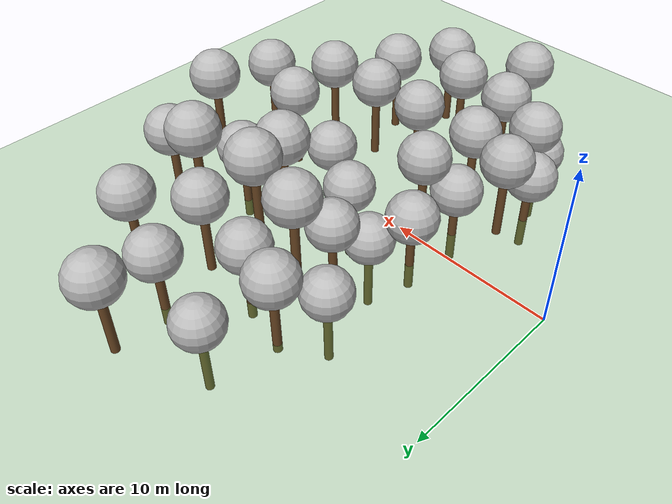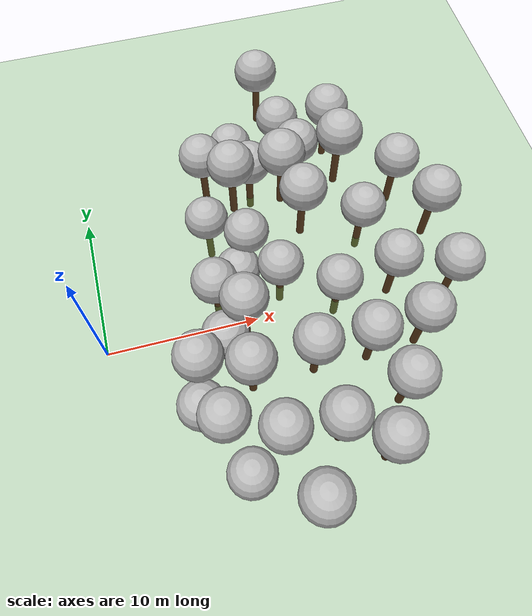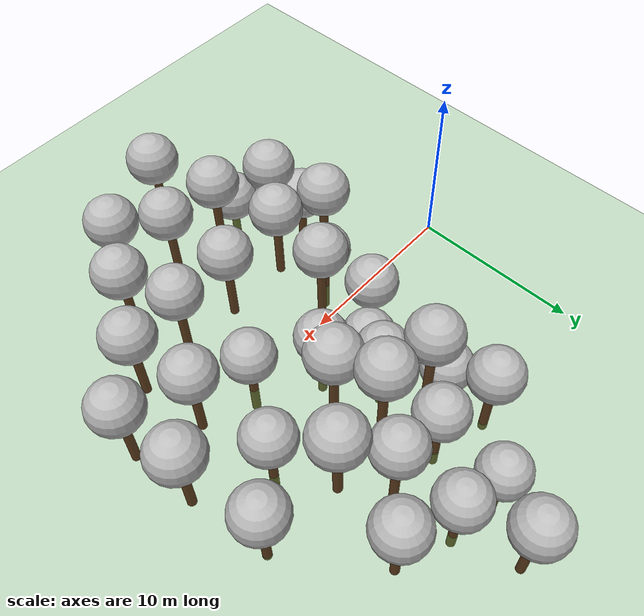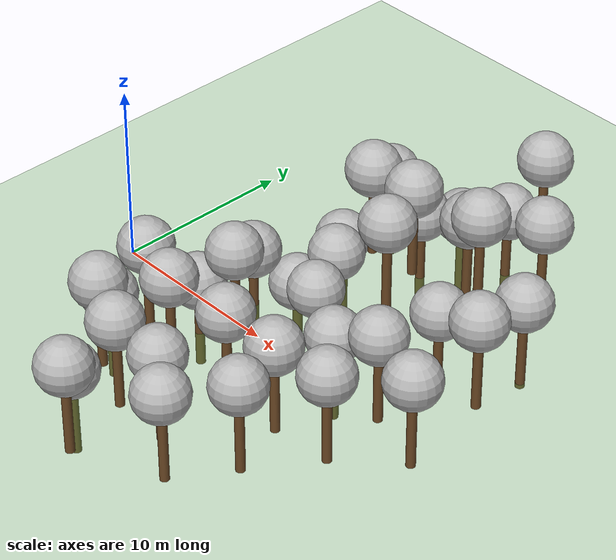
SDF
<sdf version="1.6">
 <world name="default">
  <plugin name="mrs_gazebo_static_transform_republisher_plugin" filename="libmrs_gazebo_static_transform_republisher.so"/>
  <spherical_coordinates>
   <surface_model>EARTH_WGS84</surface_model>
   <latitude_deg>37.4118</latitude_deg>
   <longitude_deg>-121.996</longitude_deg>
   <elevation>0</elevation>
   <heading_deg>0</heading_deg>
  </spherical_coordinates>
  <physics name="default_physics" default="0" type="ode">
   <ode>
    <solver>
     <type>quick</type>
     <iters>10</iters>
     <sor>1.3</sor>
     <use_dynamic_moi_rescaling>0</use_dynamic_moi_rescaling>
    </solver>
    <constraints>
     <cfm>0</cfm>
     <erp>0.2</erp>
     <contact_max_correcting_vel>1000</contact_max_correcting_vel>
     <contact_surface_layer>0.001</contact_surface_layer>
    </constraints>
   </ode>
   <max_step_size>0.004</max_step_size>
   <real_time_factor>1</real_time_factor>
   <real_time_update_rate>250</real_time_update_rate>
   <magnetic_field>6.0e-06 2.3e-05 -4.2e-05</magnetic_field>
  </physics>
  <scene><shadows>0</shadows><ambient>0.4 0.4 0.4 1</ambient><background>0.7 0.7 0.7 1</background></scene>
  <light name="sun" type="directional">
   <pose>250 250 600 0 -0 0</pose>
   <diffuse>0.8 0.8 0.8 1</diffuse>
   <specular>0.2 0.2 0.2 1</specular>
   <attenuation>
    <range>1000</range>
    <constant>0.9</constant>
    <linear>0.01</linear>
    <quadratic>0.001</quadratic>
   </attenuation>
   <direction>0 0 -1</direction>
  </light>
  <model name="ground_plane">
   <static>1</static>
   <link name="link">
    <collision name="collision">
     <geometry><plane><normal>0 0 1</normal><size>250 250</size></plane></geometry>
     <surface><friction><ode><mu>1</mu><mu2>1</mu2></ode></friction></surface>
    </collision>
    <visual name="grass">
     <cast_shadows>0</cast_shadows>
     <geometry><plane><normal>0 0 1</normal><size>150 250</size></plane></geometry>
     <material>
      <script><uri>file://media/materials/scripts/Gazebo.material</uri><name>Gazebo/Grass</name></script>
     </material>
    </visual>
   </link>
  </model>
  <gravity>0 0 -9.8066</gravity>
  <magnetic_field>6e-06 2.3e-05 -4.2e-05</magnetic_field>
  <atmosphere type="adiabatic"/>
  <model name="tree_simple">
   <static>1</static>
   <link name="link">
    <pose>0 0 0.1 0 -0 0</pose>
    <inertial>
     <mass>666</mass>
     <inertia>
      <ixx>0.0861167</ixx>
      <ixy>0</ixy>
      <ixz>0</ixz>
      <iyy>0.0861167</iyy>
      <iyz>0</iyz>
      <izz>0.0861167</izz>
     </inertia>
    </inertial>
    <collision name="collision_trunk">
     <pose>0 0 2 0 -0 0</pose>
     <geometry><cylinder><radius>0.25</radius><length>4</length></cylinder></geometry>
     <surface>
      <contact>
       <poissons_ratio>0.347</poissons_ratio>
       <elastic_modulus>8.8e+09</elastic_modulus>
       <ode><kp>100000</kp><kd>100</kd><max_vel>100</max_vel><min_depth>0.001</min_depth></ode>
      </contact>
      <friction>
       <torsional>
        <coefficient>1</coefficient>
        <use_patch_radius>0</use_patch_radius>
        <surface_radius>0.01</surface_radius>
       </torsional>
      </friction>
     </surface>
    </collision>
    <collision name="collision_treetop">
     <pose>0 0 5.2 0 -0 0</pose>
     <geometry><sphere><radius>1.5</radius></sphere></geometry>
     <surface>
      <contact>
       <poissons_ratio>0.347</poissons_ratio>
       <elastic_modulus>8.8e+09</elastic_modulus>
       <ode><kp>100000</kp><kd>100</kd><max_vel>100</max_vel><min_depth>0.001</min_depth></ode>
      </contact>
      <friction>
       <torsional>
        <coefficient>1</coefficient>
        <use_patch_radius>0</use_patch_radius>
        <surface_radius>0.01</surface_radius>
       </torsional>
      </friction>
     </surface>
    </collision>
    <visual name="trunk">
     <pose>0 0 2 0 -0 0</pose>
     <geometry><cylinder><radius>0.25</radius><length>4</length></cylinder></geometry>
     <material>
      <script>
       <uri>model://tree_simple/scripts</uri>
       <uri>model://tree_simple/materials/textures</uri>
       <name>TreeSimple/Trunk</name>
      </script>
     </material>
    </visual>
    <visual name="treetop">
     <pose>0 0 5.2 0 -0 0</pose>
     <geometry><sphere><radius>1.5</radius></sphere></geometry>
     <material>
      <script>
       <uri>model://tree_simple/scripts</uri>
       <uri>model://tree_simple/materials/textures</uri>
       <name>TreeSimple/Treetop</name>
      </script>
     </material>
    </visual>
   </link>
   <pose>5.72189 -3.56908 0 0 -0 0</pose>
  </model>
  <model name="tree_simple_0">
   <static>1</static>
   <link name="link">
    <pose>0 0 0.1 0 -0 0</pose>
    <inertial>
     <mass>666</mass>
     <inertia>
      <ixx>0.0861167</ixx>
      <ixy>0</ixy>
      <ixz>0</ixz>
      <iyy>0.0861167</iyy>
      <iyz>0</iyz>
      <izz>0.0861167</izz>
     </inertia>
    </inertial>
    <collision name="collision_trunk">
     <pose>0 0 2 0 -0 0</pose>
     <geometry><cylinder><radius>0.25</radius><length>4</length></cylinder></geometry>
     <surface>
      <contact>
       <poissons_ratio>0.347</poissons_ratio>
       <elastic_modulus>8.8e+09</elastic_modulus>
       <ode><kp>100000</kp><kd>100</kd><max_vel>100</max_vel><min_depth>0.001</min_depth></ode>
      </contact>
      <friction>
       <torsional>
        <coefficient>1</coefficient>
        <use_patch_radius>0</use_patch_radius>
        <surface_radius>0.01</surface_radius>
       </torsional>
      </friction>
     </surface>
    </collision>
    <collision name="collision_treetop">
     <pose>0 0 5.2 0 -0 0</pose>
     <geometry><sphere><radius>1.5</radius></sphere></geometry>
     <surface>
      <contact>
       <poissons_ratio>0.347</poissons_ratio>
       <elastic_modulus>8.8e+09</elastic_modulus>
       <ode><kp>100000</kp><kd>100</kd><max_vel>100</max_vel><min_depth>0.001</min_depth></ode>
      </contact>
      <friction>
       <torsional>
        <coefficient>1</coefficient>
        <use_patch_radius>0</use_patch_radius>
        <surface_radius>0.01</surface_radius>
       </torsional>
      </friction>
     </surface>
    </collision>
    <visual name="trunk">
     <pose>0 0 2 0 -0 0</pose>
     <geometry><cylinder><radius>0.25</radius><length>4</length></cylinder></geometry>
     <material>
      <script>
       <uri>model://tree_simple/scripts</uri>
       <uri>model://tree_simple/materials/textures</uri>
       <name>TreeSimple/Trunk</name>
      </script>
     </material>
    </visual>
    <visual name="treetop">
     <pose>0 0 5.2 0 -0 0</pose>
     <geometry><sphere><radius>1.5</radius></sphere></geometry>
     <material>
      <script>
       <uri>model://tree_simple/scripts</uri>
       <uri>model://tree_simple/materials/textures</uri>
       <name>TreeSimple/Treetop</name>
      </script>
     </material>
    </visual>
   </link>
   <pose>10.5264 -12.5818 0 0 -0 0</pose>
  </model>
  <model name="tree_simple_1">
   <static>1</static>
   <link name="link">
    <pose>0 0 0.1 0 -0 0</pose>
    <inertial>
     <mass>666</mass>
     <inertia>
      <ixx>0.0861167</ixx>
      <ixy>0</ixy>
      <ixz>0</ixz>
      <iyy>0.0861167</iyy>
      <iyz>0</iyz>
      <izz>0.0861167</izz>
     </inertia>
    </inertial>
    <collision name="collision_trunk">
     <pose>0 0 2 0 -0 0</pose>
     <geometry><cylinder><radius>0.25</radius><length>4</length></cylinder></geometry>
     <surface>
      <contact>
       <poissons_ratio>0.347</poissons_ratio>
       <elastic_modulus>8.8e+09</elastic_modulus>
       <ode><kp>100000</kp><kd>100</kd><max_vel>100</max_vel><min_depth>0.001</min_depth></ode>
      </contact>
      <friction>
       <torsional>
        <coefficient>1</coefficient>
        <use_patch_radius>0</use_patch_radius>
        <surface_radius>0.01</surface_radius>
       </torsional>
      </friction>
     </surface>
    </collision>
    <collision name="collision_treetop">
     <pose>0 0 5.2 0 -0 0</pose>
     <geometry><sphere><radius>1.5</radius></sphere></geometry>
     <surface>
      <contact>
       <poissons_ratio>0.347</poissons_ratio>
       <elastic_modulus>8.8e+09</elastic_modulus>
       <ode><kp>100000</kp><kd>100</kd><max_vel>100</max_vel><min_depth>0.001</min_depth></ode>
      </contact>
      <friction>
       <torsional>
        <coefficient>1</coefficient>
        <use_patch_radius>0</use_patch_radius>
        <surface_radius>0.01</surface_radius>
       </torsional>
      </friction>
     </surface>
    </collision>
    <visual name="trunk">
     <pose>0 0 2 0 -0 0</pose>
     <geometry><cylinder><radius>0.25</radius><length>4</length></cylinder></geometry>
     <material>
      <script>
       <uri>model://tree_simple/scripts</uri>
       <uri>model://tree_simple/materials/textures</uri>
       <name>TreeSimple/Trunk</name>
      </script>
     </material>
    </visual>
    <visual name="treetop">
     <pose>0 0 5.2 0 -0 0</pose>
     <geometry><sphere><radius>1.5</radius></sphere></geometry>
     <material>
      <script>
       <uri>model://tree_simple/scripts</uri>
       <uri>model://tree_simple/materials/textures</uri>
       <name>TreeSimple/Treetop</name>
      </script>
     </material>
    </visual>
   </link>
   <pose>18.1214 12.2632 0 0 -0 0</pose>
  </model>
  <model name="tree_simple_2">
   <static>1</static>
   <link name="link">
    <pose>0 0 0.1 0 -0 0</pose>
    <inertial>
     <mass>666</mass>
     <inertia>
      <ixx>0.0861167</ixx>
      <ixy>0</ixy>
      <ixz>0</ixz>
      <iyy>0.0861167</iyy>
      <iyz>0</iyz>
      <izz>0.0861167</izz>
     </inertia>
    </inertial>
    <collision name="collision_trunk">
     <pose>0 0 2 0 -0 0</pose>
     <geometry><cylinder><radius>0.25</radius><length>4</length></cylinder></geometry>
     <surface>
      <contact>
       <poissons_ratio>0.347</poissons_ratio>
       <elastic_modulus>8.8e+09</elastic_modulus>
       <ode><kp>100000</kp><kd>100</kd><max_vel>100</max_vel><min_depth>0.001</min_depth></ode>
      </contact>
      <friction>
       <torsional>
        <coefficient>1</coefficient>
        <use_patch_radius>0</use_patch_radius>
        <surface_radius>0.01</surface_radius>
       </torsional>
      </friction>
     </surface>
    </collision>
    <collision name="collision_treetop">
     <pose>0 0 5.2 0 -0 0</pose>
     <geometry><sphere><radius>1.5</radius></sphere></geometry>
     <surface>
      <contact>
       <poissons_ratio>0.347</poissons_ratio>
       <elastic_modulus>8.8e+09</elastic_modulus>
       <ode><kp>100000</kp><kd>100</kd><max_vel>100</max_vel><min_depth>0.001</min_depth></ode>
      </contact>
      <friction>
       <torsional>
        <coefficient>1</coefficient>
        <use_patch_radius>0</use_patch_radius>
        <surface_radius>0.01</surface_radius>
       </torsional>
      </friction>
     </surface>
    </collision>
    <visual name="trunk">
     <pose>0 0 2 0 -0 0</pose>
     <geometry><cylinder><radius>0.25</radius><length>4</length></cylinder></geometry>
     <material>
      <script>
       <uri>model://tree_simple/scripts</uri>
       <uri>model://tree_simple/materials/textures</uri>
       <name>TreeSimple/Trunk</name>
      </script>
     </material>
    </visual>
    <visual name="treetop">
     <pose>0 0 5.2 0 -0 0</pose>
     <geometry><sphere><radius>1.5</radius></sphere></geometry>
     <material>
      <script>
       <uri>model://tree_simple/scripts</uri>
       <uri>model://tree_simple/materials/textures</uri>
       <name>TreeSimple/Treetop</name>
      </script>
     </material>
    </visual>
   </link>
   <pose>8.26028 7.60293 -3.64952 0 -0 0</pose>
  </model>
  <model name="tree_simple_3">
   <static>1</static>
   <link name="link">
    <pose>0 0 0.1 0 -0 0</pose>
    <inertial>
     <mass>666</mass>
     <inertia>
      <ixx>0.0861167</ixx>
      <ixy>0</ixy>
      <ixz>0</ixz>
      <iyy>0.0861167</iyy>
      <iyz>0</iyz>
      <izz>0.0861167</izz>
     </inertia>
    </inertial>
    <collision name="collision_trunk">
     <pose>0 0 2 0 -0 0</pose>
     <geometry><cylinder><radius>0.25</radius><length>4</length></cylinder></geometry>
     <surface>
      <contact>
       <poissons_ratio>0.347</poissons_ratio>
       <elastic_modulus>8.8e+09</elastic_modulus>
       <ode><kp>100000</kp><kd>100</kd><max_vel>100</max_vel><min_depth>0.001</min_depth></ode>
      </contact>
      <friction>
       <torsional>
        <coefficient>1</coefficient>
        <use_patch_radius>0</use_patch_radius>
        <surface_radius>0.01</surface_radius>
       </torsional>
      </friction>
     </surface>
    </collision>
    <collision name="collision_treetop">
     <pose>0 0 5.2 0 -0 0</pose>
     <geometry><sphere><radius>1.5</radius></sphere></geometry>
     <surface>
      <contact>
       <poissons_ratio>0.347</poissons_ratio>
       <elastic_modulus>8.8e+09</elastic_modulus>
       <ode><kp>100000</kp><kd>100</kd><max_vel>100</max_vel><min_depth>0.001</min_depth></ode>
      </contact>
      <friction>
       <torsional>
        <coefficient>1</coefficient>
        <use_patch_radius>0</use_patch_radius>
        <surface_radius>0.01</surface_radius>
       </torsional>
      </friction>
     </surface>
    </collision>
    <visual name="trunk">
     <pose>0 0 2 0 -0 0</pose>
     <geometry><cylinder><radius>0.25</radius><length>4</length></cylinder></geometry>
     <material>
      <script>
       <uri>model://tree_simple/scripts</uri>
       <uri>model://tree_simple/materials/textures</uri>
       <name>TreeSimple/Trunk</name>
      </script>
     </material>
    </visual>
    <visual name="treetop">
     <pose>0 0 5.2 0 -0 0</pose>
     <geometry><sphere><radius>1.5</radius></sphere></geometry>
     <material>
      <script>
       <uri>model://tree_simple/scripts</uri>
       <uri>model://tree_simple/materials/textures</uri>
       <name>TreeSimple/Treetop</name>
      </script>
     </material>
    </visual>
   </link>
   <pose>9.46646 -8.62281 0 0 -0 0</pose>
  </model>
  <model name="tree_simple_4">
   <static>1</static>
   <link name="link">
    <pose>0 0 0.1 0 -0 0</pose>
    <inertial>
     <mass>666</mass>
     <inertia>
      <ixx>0.0861167</ixx>
      <ixy>0</ixy>
      <ixz>0</ixz>
      <iyy>0.0861167</iyy>
      <iyz>0</iyz>
      <izz>0.0861167</izz>
     </inertia>
    </inertial>
    <collision name="collision_trunk">
     <pose>0 0 2 0 -0 0</pose>
     <geometry><cylinder><radius>0.25</radius><length>4</length></cylinder></geometry>
     <surface>
      <contact>
       <poissons_ratio>0.347</poissons_ratio>
       <elastic_modulus>8.8e+09</elastic_modulus>
       <ode><kp>100000</kp><kd>100</kd><max_vel>100</max_vel><min_depth>0.001</min_depth></ode>
      </contact>
      <friction>
       <torsional>
        <coefficient>1</coefficient>
        <use_patch_radius>0</use_patch_radius>
        <surface_radius>0.01</surface_radius>
       </torsional>
      </friction>
     </surface>
    </collision>
    <collision name="collision_treetop">
     <pose>0 0 5.2 0 -0 0</pose>
     <geometry><sphere><radius>1.5</radius></sphere></geometry>
     <surface>
      <contact>
       <poissons_ratio>0.347</poissons_ratio>
       <elastic_modulus>8.8e+09</elastic_modulus>
       <ode><kp>100000</kp><kd>100</kd><max_vel>100</max_vel><min_depth>0.001</min_depth></ode>
      </contact>
      <friction>
       <torsional>
        <coefficient>1</coefficient>
        <use_patch_radius>0</use_patch_radius>
        <surface_radius>0.01</surface_radius>
       </torsional>
      </friction>
     </surface>
    </collision>
    <visual name="trunk">
     <pose>0 0 2 0 -0 0</pose>
     <geometry><cylinder><radius>0.25</radius><length>4</length></cylinder></geometry>
     <material>
      <script>
       <uri>model://tree_simple/scripts</uri>
       <uri>model://tree_simple/materials/textures</uri>
       <name>TreeSimple/Trunk</name>
      </script>
     </material>
    </visual>
    <visual name="treetop">
     <pose>0 0 5.2 0 -0 0</pose>
     <geometry><sphere><radius>1.5</radius></sphere></geometry>
     <material>
      <script>
       <uri>model://tree_simple/scripts</uri>
       <uri>model://tree_simple/materials/textures</uri>
       <name>TreeSimple/Treetop</name>
      </script>
     </material>
    </visual>
   </link>
   <pose>15.196 -10.5861 0 0 -0 0</pose>
  </model>
  <model name="tree_simple_5">
   <static>1</static>
   <link name="link">
    <pose>0 0 0.1 0 -0 0</pose>
    <inertial>
     <mass>666</mass>
     <inertia>
      <ixx>0.0861167</ixx>
      <ixy>0</ixy>
      <ixz>0</ixz>
      <iyy>0.0861167</iyy>
      <iyz>0</iyz>
      <izz>0.0861167</izz>
     </inertia>
    </inertial>
    <collision name="collision_trunk">
     <pose>0 0 2 0 -0 0</pose>
     <geometry><cylinder><radius>0.25</radius><length>4</length></cylinder></geometry>
     <surface>
      <contact>
       <poissons_ratio>0.347</poissons_ratio>
       <elastic_modulus>8.8e+09</elastic_modulus>
       <ode><kp>100000</kp><kd>100</kd><max_vel>100</max_vel><min_depth>0.001</min_depth></ode>
      </contact>
      <friction>
       <torsional>
        <coefficient>1</coefficient>
        <use_patch_radius>0</use_patch_radius>
        <surface_radius>0.01</surface_radius>
       </torsional>
      </friction>
     </surface>
    </collision>
    <collision name="collision_treetop">
     <pose>0 0 5.2 0 -0 0</pose>
     <geometry><sphere><radius>1.5</radius></sphere></geometry>
     <surface>
      <contact>
       <poissons_ratio>0.347</poissons_ratio>
       <elastic_modulus>8.8e+09</elastic_modulus>
       <ode><kp>100000</kp><kd>100</kd><max_vel>100</max_vel><min_depth>0.001</min_depth></ode>
      </contact>
      <friction>
       <torsional>
        <coefficient>1</coefficient>
        <use_patch_radius>0</use_patch_radius>
        <surface_radius>0.01</surface_radius>
       </torsional>
      </friction>
     </surface>
    </collision>
    <visual name="trunk">
     <pose>0 0 2 0 -0 0</pose>
     <geometry><cylinder><radius>0.25</radius><length>4</length></cylinder></geometry>
     <material>
      <script>
       <uri>model://tree_simple/scripts</uri>
       <uri>model://tree_simple/materials/textures</uri>
       <name>TreeSimple/Trunk</name>
      </script>
     </material>
    </visual>
    <visual name="treetop">
     <pose>0 0 5.2 0 -0 0</pose>
     <geometry><sphere><radius>1.5</radius></sphere></geometry>
     <material>
      <script>
       <uri>model://tree_simple/scripts</uri>
       <uri>model://tree_simple/materials/textures</uri>
       <name>TreeSimple/Treetop</name>
      </script>
     </material>
    </visual>
   </link>
   <pose>9.09139 -0.673957 0 0 -0 0</pose>
  </model>
  <model name="tree_simple_6">
   <static>1</static>
   <link name="link">
    <pose>0 0 0.1 0 -0 0</pose>
    <inertial>
     <mass>666</mass>
     <inertia>
      <ixx>0.0861167</ixx>
      <ixy>0</ixy>
      <ixz>0</ixz>
      <iyy>0.0861167</iyy>
      <iyz>0</iyz>
      <izz>0.0861167</izz>
     </inertia>
    </inertial>
    <collision name="collision_trunk">
     <pose>0 0 2 0 -0 0</pose>
     <geometry><cylinder><radius>0.25</radius><length>4</length></cylinder></geometry>
     <surface>
      <contact>
       <poissons_ratio>0.347</poissons_ratio>
       <elastic_modulus>8.8e+09</elastic_modulus>
       <ode><kp>100000</kp><kd>100</kd><max_vel>100</max_vel><min_depth>0.001</min_depth></ode>
      </contact>
      <friction>
       <torsional>
        <coefficient>1</coefficient>
        <use_patch_radius>0</use_patch_radius>
        <surface_radius>0.01</surface_radius>
       </torsional>
      </friction>
     </surface>
    </collision>
    <collision name="collision_treetop">
     <pose>0 0 5.2 0 -0 0</pose>
     <geometry><sphere><radius>1.5</radius></sphere></geometry>
     <surface>
      <contact>
       <poissons_ratio>0.347</poissons_ratio>
       <elastic_modulus>8.8e+09</elastic_modulus>
       <ode><kp>100000</kp><kd>100</kd><max_vel>100</max_vel><min_depth>0.001</min_depth></ode>
      </contact>
      <friction>
       <torsional>
        <coefficient>1</coefficient>
        <use_patch_radius>0</use_patch_radius>
        <surface_radius>0.01</surface_radius>
       </torsional>
      </friction>
     </surface>
    </collision>
    <visual name="trunk">
     <pose>0 0 2 0 -0 0</pose>
     <geometry><cylinder><radius>0.25</radius><length>4</length></cylinder></geometry>
     <material>
      <script>
       <uri>model://tree_simple/scripts</uri>
       <uri>model://tree_simple/materials/textures</uri>
       <name>TreeSimple/Trunk</name>
      </script>
     </material>
    </visual>
    <visual name="treetop">
     <pose>0 0 5.2 0 -0 0</pose>
     <geometry><sphere><radius>1.5</radius></sphere></geometry>
     <material>
      <script>
       <uri>model://tree_simple/scripts</uri>
       <uri>model://tree_simple/materials/textures</uri>
       <name>TreeSimple/Treetop</name>
      </script>
     </material>
    </visual>
   </link>
   <pose>12.8258 -8.77731 0 0 -0 0</pose>
  </model>
  <model name="tree_simple_7">
   <static>1</static>
   <link name="link">
    <pose>0 0 0.1 0 -0 0</pose>
    <inertial>
     <mass>666</mass>
     <inertia>
      <ixx>0.0861167</ixx>
      <ixy>0</ixy>
      <ixz>0</ixz>
      <iyy>0.0861167</iyy>
      <iyz>0</iyz>
      <izz>0.0861167</izz>
     </inertia>
    </inertial>
    <collision name="collision_trunk">
     <pose>0 0 2 0 -0 0</pose>
     <geometry><cylinder><radius>0.25</radius><length>4</length></cylinder></geometry>
     <surface>
      <contact>
       <poissons_ratio>0.347</poissons_ratio>
       <elastic_modulus>8.8e+09</elastic_modulus>
       <ode><kp>100000</kp><kd>100</kd><max_vel>100</max_vel><min_depth>0.001</min_depth></ode>
      </contact>
      <friction>
       <torsional>
        <coefficient>1</coefficient>
        <use_patch_radius>0</use_patch_radius>
        <surface_radius>0.01</surface_radius>
       </torsional>
      </friction>
     </surface>
    </collision>
    <collision name="collision_treetop">
     <pose>0 0 5.2 0 -0 0</pose>
     <geometry><sphere><radius>1.5</radius></sphere></geometry>
     <surface>
      <contact>
       <poissons_ratio>0.347</poissons_ratio>
       <elastic_modulus>8.8e+09</elastic_modulus>
       <ode><kp>100000</kp><kd>100</kd><max_vel>100</max_vel><min_depth>0.001</min_depth></ode>
      </contact>
      <friction>
       <torsional>
        <coefficient>1</coefficient>
        <use_patch_radius>0</use_patch_radius>
        <surface_radius>0.01</surface_radius>
       </torsional>
      </friction>
     </surface>
    </collision>
    <visual name="trunk">
     <pose>0 0 2 0 -0 0</pose>
     <geometry><cylinder><radius>0.25</radius><length>4</length></cylinder></geometry>
     <material>
      <script>
       <uri>model://tree_simple/scripts</uri>
       <uri>model://tree_simple/materials/textures</uri>
       <name>TreeSimple/Trunk</name>
      </script>
     </material>
    </visual>
    <visual name="treetop">
     <pose>0 0 5.2 0 -0 0</pose>
     <geometry><sphere><radius>1.5</radius></sphere></geometry>
     <material>
      <script>
       <uri>model://tree_simple/scripts</uri>
       <uri>model://tree_simple/materials/textures</uri>
       <name>TreeSimple/Treetop</name>
      </script>
     </material>
    </visual>
   </link>
   <pose>12.5972 -4.31424 0 0 -0 0</pose>
  </model>
  <model name="tree_simple_8">
   <static>1</static>
   <link name="link">
    <pose>0 0 0.1 0 -0 0</pose>
    <inertial>
     <mass>666</mass>
     <inertia>
      <ixx>0.0861167</ixx>
      <ixy>0</ixy>
      <ixz>0</ixz>
      <iyy>0.0861167</iyy>
      <iyz>0</iyz>
      <izz>0.0861167</izz>
     </inertia>
    </inertial>
    <collision name="collision_trunk">
     <pose>0 0 2 0 -0 0</pose>
     <geometry><cylinder><radius>0.25</radius><length>4</length></cylinder></geometry>
     <surface>
      <contact>
       <poissons_ratio>0.347</poissons_ratio>
       <elastic_modulus>8.8e+09</elastic_modulus>
       <ode><kp>100000</kp><kd>100</kd><max_vel>100</max_vel><min_depth>0.001</min_depth></ode>
      </contact>
      <friction>
       <torsional>
        <coefficient>1</coefficient>
        <use_patch_radius>0</use_patch_radius>
        <surface_radius>0.01</surface_radius>
       </torsional>
      </friction>
     </surface>
    </collision>
    <collision name="collision_treetop">
     <pose>0 0 5.2 0 -0 0</pose>
     <geometry><sphere><radius>1.5</radius></sphere></geometry>
     <surface>
      <contact>
       <poissons_ratio>0.347</poissons_ratio>
       <elastic_modulus>8.8e+09</elastic_modulus>
       <ode><kp>100000</kp><kd>100</kd><max_vel>100</max_vel><min_depth>0.001</min_depth></ode>
      </contact>
      <friction>
       <torsional>
        <coefficient>1</coefficient>
        <use_patch_radius>0</use_patch_radius>
        <surface_radius>0.01</surface_radius>
       </torsional>
      </friction>
     </surface>
    </collision>
    <visual name="trunk">
     <pose>0 0 2 0 -0 0</pose>
     <geometry><cylinder><radius>0.25</radius><length>4</length></cylinder></geometry>
     <material>
      <script>
       <uri>model://tree_simple/scripts</uri>
       <uri>model://tree_simple/materials/textures</uri>
       <name>TreeSimple/Trunk</name>
      </script>
     </material>
    </visual>
    <visual name="treetop">
     <pose>0 0 5.2 0 -0 0</pose>
     <geometry><sphere><radius>1.5</radius></sphere></geometry>
     <material>
      <script>
       <uri>model://tree_simple/scripts</uri>
       <uri>model://tree_simple/materials/textures</uri>
       <name>TreeSimple/Treetop</name>
      </script>
     </material>
    </visual>
   </link>
   <pose>6.40844 -7.20661 0 0 -0 0</pose>
  </model>
  <model name="tree_simple_9">
   <static>1</static>
   <link name="link">
    <pose>0 0 0.1 0 -0 0</pose>
    <inertial>
     <mass>666</mass>
     <inertia>
      <ixx>0.0861167</ixx>
      <ixy>0</ixy>
      <ixz>0</ixz>
      <iyy>0.0861167</iyy>
      <iyz>0</iyz>
      <izz>0.0861167</izz>
     </inertia>
    </inertial>
    <collision name="collision_trunk">
     <pose>0 0 2 0 -0 0</pose>
     <geometry><cylinder><radius>0.25</radius><length>4</length></cylinder></geometry>
     <surface>
      <contact>
       <poissons_ratio>0.347</poissons_ratio>
       <elastic_modulus>8.8e+09</elastic_modulus>
       <ode><kp>100000</kp><kd>100</kd><max_vel>100</max_vel><min_depth>0.001</min_depth></ode>
      </contact>
      <friction>
       <torsional>
        <coefficient>1</coefficient>
        <use_patch_radius>0</use_patch_radius>
        <surface_radius>0.01</surface_radius>
       </torsional>
      </friction>
     </surface>
    </collision>
    <collision name="collision_treetop">
     <pose>0 0 5.2 0 -0 0</pose>
     <geometry><sphere><radius>1.5</radius></sphere></geometry>
     <surface>
      <contact>
       <poissons_ratio>0.347</poissons_ratio>
       <elastic_modulus>8.8e+09</elastic_modulus>
       <ode><kp>100000</kp><kd>100</kd><max_vel>100</max_vel><min_depth>0.001</min_depth></ode>
      </contact>
      <friction>
       <torsional>
        <coefficient>1</coefficient>
        <use_patch_radius>0</use_patch_radius>
        <surface_radius>0.01</surface_radius>
       </torsional>
      </friction>
     </surface>
    </collision>
    <visual name="trunk">
     <pose>0 0 2 0 -0 0</pose>
     <geometry><cylinder><radius>0.25</radius><length>4</length></cylinder></geometry>
     <material>
      <script>
       <uri>model://tree_simple/scripts</uri>
       <uri>model://tree_simple/materials/textures</uri>
       <name>TreeSimple/Trunk</name>
      </script>
     </material>
    </visual>
    <visual name="treetop">
     <pose>0 0 5.2 0 -0 0</pose>
     <geometry><sphere><radius>1.5</radius></sphere></geometry>
     <material>
      <script>
       <uri>model://tree_simple/scripts</uri>
       <uri>model://tree_simple/materials/textures</uri>
       <name>TreeSimple/Treetop</name>
      </script>
     </material>
    </visual>
   </link>
   <pose>17.161 -7.52811 0 0 -0 0</pose>
  </model>
  <model name="tree_simple_10">
   <static>1</static>
   <link name="link">
    <pose>0 0 0.1 0 -0 0</pose>
    <inertial>
     <mass>666</mass>
     <inertia>
      <ixx>0.0861167</ixx>
      <ixy>0</ixy>
      <ixz>0</ixz>
      <iyy>0.0861167</iyy>
      <iyz>0</iyz>
      <izz>0.0861167</izz>
     </inertia>
    </inertial>
    <collision name="collision_trunk">
     <pose>0 0 2 0 -0 0</pose>
     <geometry><cylinder><radius>0.25</radius><length>4</length></cylinder></geometry>
     <surface>
      <contact>
       <poissons_ratio>0.347</poissons_ratio>
       <elastic_modulus>8.8e+09</elastic_modulus>
       <ode><kp>100000</kp><kd>100</kd><max_vel>100</max_vel><min_depth>0.001</min_depth></ode>
      </contact>
      <friction>
       <torsional>
        <coefficient>1</coefficient>
        <use_patch_radius>0</use_patch_radius>
        <surface_radius>0.01</surface_radius>
       </torsional>
      </friction>
     </surface>
    </collision>
    <collision name="collision_treetop">
     <pose>0 0 5.2 0 -0 0</pose>
     <geometry><sphere><radius>1.5</radius></sphere></geometry>
     <surface>
      <contact>
       <poissons_ratio>0.347</poissons_ratio>
       <elastic_modulus>8.8e+09</elastic_modulus>
       <ode><kp>100000</kp><kd>100</kd><max_vel>100</max_vel><min_depth>0.001</min_depth></ode>
      </contact>
      <friction>
       <torsional>
        <coefficient>1</coefficient>
        <use_patch_radius>0</use_patch_radius>
        <surface_radius>0.01</surface_radius>
       </torsional>
      </friction>
     </surface>
    </collision>
    <visual name="trunk">
     <pose>0 0 2 0 -0 0</pose>
     <geometry><cylinder><radius>0.25</radius><length>4</length></cylinder></geometry>
     <material>
      <script>
       <uri>model://tree_simple/scripts</uri>
       <uri>model://tree_simple/materials/textures</uri>
       <name>TreeSimple/Trunk</name>
      </script>
     </material>
    </visual>
    <visual name="treetop">
     <pose>0 0 5.2 0 -0 0</pose>
     <geometry><sphere><radius>1.5</radius></sphere></geometry>
     <material>
      <script>
       <uri>model://tree_simple/scripts</uri>
       <uri>model://tree_simple/materials/textures</uri>
       <name>TreeSimple/Treetop</name>
      </script>
     </material>
    </visual>
   </link>
   <pose>19.4597 -4.05165 0 0 -0 0</pose>
  </model>
  <model name="tree_simple_11">
   <static>1</static>
   <link name="link">
    <pose>0 0 0.1 0 -0 0</pose>
    <inertial>
     <mass>666</mass>
     <inertia>
      <ixx>0.0861167</ixx>
      <ixy>0</ixy>
      <ixz>0</ixz>
      <iyy>0.0861167</iyy>
      <iyz>0</iyz>
      <izz>0.0861167</izz>
     </inertia>
    </inertial>
    <collision name="collision_trunk">
     <pose>0 0 2 0 -0 0</pose>
     <geometry><cylinder><radius>0.25</radius><length>4</length></cylinder></geometry>
     <surface>
      <contact>
       <poissons_ratio>0.347</poissons_ratio>
       <elastic_modulus>8.8e+09</elastic_modulus>
       <ode><kp>100000</kp><kd>100</kd><max_vel>100</max_vel><min_depth>0.001</min_depth></ode>
      </contact>
      <friction>
       <torsional>
        <coefficient>1</coefficient>
        <use_patch_radius>0</use_patch_radius>
        <surface_radius>0.01</surface_radius>
       </torsional>
      </friction>
     </surface>
    </collision>
    <collision name="collision_treetop">
     <pose>0 0 5.2 0 -0 0</pose>
     <geometry><sphere><radius>1.5</radius></sphere></geometry>
     <surface>
      <contact>
       <poissons_ratio>0.347</poissons_ratio>
       <elastic_modulus>8.8e+09</elastic_modulus>
       <ode><kp>100000</kp><kd>100</kd><max_vel>100</max_vel><min_depth>0.001</min_depth></ode>
      </contact>
      <friction>
       <torsional>
        <coefficient>1</coefficient>
        <use_patch_radius>0</use_patch_radius>
        <surface_radius>0.01</surface_radius>
       </torsional>
      </friction>
     </surface>
    </collision>
    <visual name="trunk">
     <pose>0 0 2 0 -0 0</pose>
     <geometry><cylinder><radius>0.25</radius><length>4</length></cylinder></geometry>
     <material>
      <script>
       <uri>model://tree_simple/scripts</uri>
       <uri>model://tree_simple/materials/textures</uri>
       <name>TreeSimple/Trunk</name>
      </script>
     </material>
    </visual>
    <visual name="treetop">
     <pose>0 0 5.2 0 -0 0</pose>
     <geometry><sphere><radius>1.5</radius></sphere></geometry>
     <material>
      <script>
       <uri>model://tree_simple/scripts</uri>
       <uri>model://tree_simple/materials/textures</uri>
       <name>TreeSimple/Treetop</name>
      </script>
     </material>
    </visual>
   </link>
   <pose>14.0945 16.6625 0 0 -0 0</pose>
  </model>
  <model name="tree_simple_12">
   <static>1</static>
   <link name="link">
    <pose>0 0 0.1 0 -0 0</pose>
    <inertial>
     <mass>666</mass>
     <inertia>
      <ixx>0.0861167</ixx>
      <ixy>0</ixy>
      <ixz>0</ixz>
      <iyy>0.0861167</iyy>
      <iyz>0</iyz>
      <izz>0.0861167</izz>
     </inertia>
    </inertial>
    <collision name="collision_trunk">
     <pose>0 0 2 0 -0 0</pose>
     <geometry><cylinder><radius>0.25</radius><length>4</length></cylinder></geometry>
     <surface>
      <contact>
       <poissons_ratio>0.347</poissons_ratio>
       <elastic_modulus>8.8e+09</elastic_modulus>
       <ode><kp>100000</kp><kd>100</kd><max_vel>100</max_vel><min_depth>0.001</min_depth></ode>
      </contact>
      <friction>
       <torsional>
        <coefficient>1</coefficient>
        <use_patch_radius>0</use_patch_radius>
        <surface_radius>0.01</surface_radius>
       </torsional>
      </friction>
     </surface>
    </collision>
    <collision name="collision_treetop">
     <pose>0 0 5.2 0 -0 0</pose>
     <geometry><sphere><radius>1.5</radius></sphere></geometry>
     <surface>
      <contact>
       <poissons_ratio>0.347</poissons_ratio>
       <elastic_modulus>8.8e+09</elastic_modulus>
       <ode><kp>100000</kp><kd>100</kd><max_vel>100</max_vel><min_depth>0.001</min_depth></ode>
      </contact>
      <friction>
       <torsional>
        <coefficient>1</coefficient>
        <use_patch_radius>0</use_patch_radius>
        <surface_radius>0.01</surface_radius>
       </torsional>
      </friction>
     </surface>
    </collision>
    <visual name="trunk">
     <pose>0 0 2 0 -0 0</pose>
     <geometry><cylinder><radius>0.25</radius><length>4</length></cylinder></geometry>
     <material>
      <script>
       <uri>model://tree_simple/scripts</uri>
       <uri>model://tree_simple/materials/textures</uri>
       <name>TreeSimple/Trunk</name>
      </script>
     </material>
    </visual>
    <visual name="treetop">
     <pose>0 0 5.2 0 -0 0</pose>
     <geometry><sphere><radius>1.5</radius></sphere></geometry>
     <material>
      <script>
       <uri>model://tree_simple/scripts</uri>
       <uri>model://tree_simple/materials/textures</uri>
       <name>TreeSimple/Treetop</name>
      </script>
     </material>
    </visual>
   </link>
   <pose>11.8716 9.75891 -1.275 0 -0 0</pose>
  </model>
  <model name="tree_simple_13">
   <static>1</static>
   <link name="link">
    <pose>0 0 0.1 0 -0 0</pose>
    <inertial>
     <mass>666</mass>
     <inertia>
      <ixx>0.0861167</ixx>
      <ixy>0</ixy>
      <ixz>0</ixz>
      <iyy>0.0861167</iyy>
      <iyz>0</iyz>
      <izz>0.0861167</izz>
     </inertia>
    </inertial>
    <collision name="collision_trunk">
     <pose>0 0 2 0 -0 0</pose>
     <geometry><cylinder><radius>0.25</radius><length>4</length></cylinder></geometry>
     <surface>
      <contact>
       <poissons_ratio>0.347</poissons_ratio>
       <elastic_modulus>8.8e+09</elastic_modulus>
       <ode><kp>100000</kp><kd>100</kd><max_vel>100</max_vel><min_depth>0.001</min_depth></ode>
      </contact>
      <friction>
       <torsional>
        <coefficient>1</coefficient>
        <use_patch_radius>0</use_patch_radius>
        <surface_radius>0.01</surface_radius>
       </torsional>
      </friction>
     </surface>
    </collision>
    <collision name="collision_treetop">
     <pose>0 0 5.2 0 -0 0</pose>
     <geometry><sphere><radius>1.5</radius></sphere></geometry>
     <surface>
      <contact>
       <poissons_ratio>0.347</poissons_ratio>
       <elastic_modulus>8.8e+09</elastic_modulus>
       <ode><kp>100000</kp><kd>100</kd><max_vel>100</max_vel><min_depth>0.001</min_depth></ode>
      </contact>
      <friction>
       <torsional>
        <coefficient>1</coefficient>
        <use_patch_radius>0</use_patch_radius>
        <surface_radius>0.01</surface_radius>
       </torsional>
      </friction>
     </surface>
    </collision>
    <visual name="trunk">
     <pose>0 0 2 0 -0 0</pose>
     <geometry><cylinder><radius>0.25</radius><length>4</length></cylinder></geometry>
     <material>
      <script>
       <uri>model://tree_simple/scripts</uri>
       <uri>model://tree_simple/materials/textures</uri>
       <name>TreeSimple/Trunk</name>
      </script>
     </material>
    </visual>
    <visual name="treetop">
     <pose>0 0 5.2 0 -0 0</pose>
     <geometry><sphere><radius>1.5</radius></sphere></geometry>
     <material>
      <script>
       <uri>model://tree_simple/scripts</uri>
       <uri>model://tree_simple/materials/textures</uri>
       <name>TreeSimple/Treetop</name>
      </script>
     </material>
    </visual>
   </link>
   <pose>10.5318 4.98436 -2.12992 0 -0 0</pose>
  </model>
  <model name="tree_simple_14">
   <static>1</static>
   <link name="link">
    <pose>0 0 0.1 0 -0 0</pose>
    <inertial>
     <mass>666</mass>
     <inertia>
      <ixx>0.0861167</ixx>
      <ixy>0</ixy>
      <ixz>0</ixz>
      <iyy>0.0861167</iyy>
      <iyz>0</iyz>
      <izz>0.0861167</izz>
     </inertia>
    </inertial>
    <collision name="collision_trunk">
     <pose>0 0 2 0 -0 0</pose>
     <geometry><cylinder><radius>0.25</radius><length>4</length></cylinder></geometry>
     <surface>
      <contact>
       <poissons_ratio>0.347</poissons_ratio>
       <elastic_modulus>8.8e+09</elastic_modulus>
       <ode><kp>100000</kp><kd>100</kd><max_vel>100</max_vel><min_depth>0.001</min_depth></ode>
      </contact>
      <friction>
       <torsional>
        <coefficient>1</coefficient>
        <use_patch_radius>0</use_patch_radius>
        <surface_radius>0.01</surface_radius>
       </torsional>
      </friction>
     </surface>
    </collision>
    <collision name="collision_treetop">
     <pose>0 0 5.2 0 -0 0</pose>
     <geometry><sphere><radius>1.5</radius></sphere></geometry>
     <surface>
      <contact>
       <poissons_ratio>0.347</poissons_ratio>
       <elastic_modulus>8.8e+09</elastic_modulus>
       <ode><kp>100000</kp><kd>100</kd><max_vel>100</max_vel><min_depth>0.001</min_depth></ode>
      </contact>
      <friction>
       <torsional>
        <coefficient>1</coefficient>
        <use_patch_radius>0</use_patch_radius>
        <surface_radius>0.01</surface_radius>
       </torsional>
      </friction>
     </surface>
    </collision>
    <visual name="trunk">
     <pose>0 0 2 0 -0 0</pose>
     <geometry><cylinder><radius>0.25</radius><length>4</length></cylinder></geometry>
     <material>
      <script>
       <uri>model://tree_simple/scripts</uri>
       <uri>model://tree_simple/materials/textures</uri>
       <name>TreeSimple/Trunk</name>
      </script>
     </material>
    </visual>
    <visual name="treetop">
     <pose>0 0 5.2 0 -0 0</pose>
     <geometry><sphere><radius>1.5</radius></sphere></geometry>
     <material>
      <script>
       <uri>model://tree_simple/scripts</uri>
       <uri>model://tree_simple/materials/textures</uri>
       <name>TreeSimple/Treetop</name>
      </script>
     </material>
    </visual>
   </link>
   <pose>22.4121 3.0458 1.13672 0 -0 0</pose>
  </model>
  <model name="tree_simple_15">
   <static>1</static>
   <link name="link">
    <pose>0 0 0.1 0 -0 0</pose>
    <inertial>
     <mass>666</mass>
     <inertia>
      <ixx>0.0861167</ixx>
      <ixy>0</ixy>
      <ixz>0</ixz>
      <iyy>0.0861167</iyy>
      <iyz>0</iyz>
      <izz>0.0861167</izz>
     </inertia>
    </inertial>
    <collision name="collision_trunk">
     <pose>0 0 2 0 -0 0</pose>
     <geometry><cylinder><radius>0.25</radius><length>4</length></cylinder></geometry>
     <surface>
      <contact>
       <poissons_ratio>0.347</poissons_ratio>
       <elastic_modulus>8.8e+09</elastic_modulus>
       <ode><kp>100000</kp><kd>100</kd><max_vel>100</max_vel><min_depth>0.001</min_depth></ode>
      </contact>
      <friction>
       <torsional>
        <coefficient>1</coefficient>
        <use_patch_radius>0</use_patch_radius>
        <surface_radius>0.01</surface_radius>
       </torsional>
      </friction>
     </surface>
    </collision>
    <collision name="collision_treetop">
     <pose>0 0 5.2 0 -0 0</pose>
     <geometry><sphere><radius>1.5</radius></sphere></geometry>
     <surface>
      <contact>
       <poissons_ratio>0.347</poissons_ratio>
       <elastic_modulus>8.8e+09</elastic_modulus>
       <ode><kp>100000</kp><kd>100</kd><max_vel>100</max_vel><min_depth>0.001</min_depth></ode>
      </contact>
      <friction>
       <torsional>
        <coefficient>1</coefficient>
        <use_patch_radius>0</use_patch_radius>
        <surface_radius>0.01</surface_radius>
       </torsional>
      </friction>
     </surface>
    </collision>
    <visual name="trunk">
     <pose>0 0 2 0 -0 0</pose>
     <geometry><cylinder><radius>0.25</radius><length>4</length></cylinder></geometry>
     <material>
      <script>
       <uri>model://tree_simple/scripts</uri>
       <uri>model://tree_simple/materials/textures</uri>
       <name>TreeSimple/Trunk</name>
      </script>
     </material>
    </visual>
    <visual name="treetop">
     <pose>0 0 5.2 0 -0 0</pose>
     <geometry><sphere><radius>1.5</radius></sphere></geometry>
     <material>
      <script>
       <uri>model://tree_simple/scripts</uri>
       <uri>model://tree_simple/materials/textures</uri>
       <name>TreeSimple/Treetop</name>
      </script>
     </material>
    </visual>
   </link>
   <pose>14.7769 13.2103 -1.35046 0 -0 0</pose>
  </model>
  <model name="tree_simple_16">
   <static>1</static>
   <link name="link">
    <pose>0 0 0.1 0 -0 0</pose>
    <inertial>
     <mass>666</mass>
     <inertia>
      <ixx>0.0861167</ixx>
      <ixy>0</ixy>
      <ixz>0</ixz>
      <iyy>0.0861167</iyy>
      <iyz>0</iyz>
      <izz>0.0861167</izz>
     </inertia>
    </inertial>
    <collision name="collision_trunk">
     <pose>0 0 2 0 -0 0</pose>
     <geometry><cylinder><radius>0.25</radius><length>4</length></cylinder></geometry>
     <surface>
      <contact>
       <poissons_ratio>0.347</poissons_ratio>
       <elastic_modulus>8.8e+09</elastic_modulus>
       <ode><kp>100000</kp><kd>100</kd><max_vel>100</max_vel><min_depth>0.001</min_depth></ode>
      </contact>
      <friction>
       <torsional>
        <coefficient>1</coefficient>
        <use_patch_radius>0</use_patch_radius>
        <surface_radius>0.01</surface_radius>
       </torsional>
      </friction>
     </surface>
    </collision>
    <collision name="collision_treetop">
     <pose>0 0 5.2 0 -0 0</pose>
     <geometry><sphere><radius>1.5</radius></sphere></geometry>
     <surface>
      <contact>
       <poissons_ratio>0.347</poissons_ratio>
       <elastic_modulus>8.8e+09</elastic_modulus>
       <ode><kp>100000</kp><kd>100</kd><max_vel>100</max_vel><min_depth>0.001</min_depth></ode>
      </contact>
      <friction>
       <torsional>
        <coefficient>1</coefficient>
        <use_patch_radius>0</use_patch_radius>
        <surface_radius>0.01</surface_radius>
       </torsional>
      </friction>
     </surface>
    </collision>
    <visual name="trunk">
     <pose>0 0 2 0 -0 0</pose>
     <geometry><cylinder><radius>0.25</radius><length>4</length></cylinder></geometry>
     <material>
      <script>
       <uri>model://tree_simple/scripts</uri>
       <uri>model://tree_simple/materials/textures</uri>
       <name>TreeSimple/Trunk</name>
      </script>
     </material>
    </visual>
    <visual name="treetop">
     <pose>0 0 5.2 0 -0 0</pose>
     <geometry><sphere><radius>1.5</radius></sphere></geometry>
     <material>
      <script>
       <uri>model://tree_simple/scripts</uri>
       <uri>model://tree_simple/materials/textures</uri>
       <name>TreeSimple/Treetop</name>
      </script>
     </material>
    </visual>
   </link>
   <pose>8.59035 -4.49916 0 0 -0 0</pose>
  </model>
  <model name="tree_simple_17">
   <static>1</static>
   <link name="link">
    <pose>0 0 0.1 0 -0 0</pose>
    <inertial>
     <mass>666</mass>
     <inertia>
      <ixx>0.0861167</ixx>
      <ixy>0</ixy>
      <ixz>0</ixz>
      <iyy>0.0861167</iyy>
      <iyz>0</iyz>
      <izz>0.0861167</izz>
     </inertia>
    </inertial>
    <collision name="collision_trunk">
     <pose>0 0 2 0 -0 0</pose>
     <geometry><cylinder><radius>0.25</radius><length>4</length></cylinder></geometry>
     <surface>
      <contact>
       <poissons_ratio>0.347</poissons_ratio>
       <elastic_modulus>8.8e+09</elastic_modulus>
       <ode><kp>100000</kp><kd>100</kd><max_vel>100</max_vel><min_depth>0.001</min_depth></ode>
      </contact>
      <friction>
       <torsional>
        <coefficient>1</coefficient>
        <use_patch_radius>0</use_patch_radius>
        <surface_radius>0.01</surface_radius>
       </torsional>
      </friction>
     </surface>
    </collision>
    <collision name="collision_treetop">
     <pose>0 0 5.2 0 -0 0</pose>
     <geometry><sphere><radius>1.5</radius></sphere></geometry>
     <surface>
      <contact>
       <poissons_ratio>0.347</poissons_ratio>
       <elastic_modulus>8.8e+09</elastic_modulus>
       <ode><kp>100000</kp><kd>100</kd><max_vel>100</max_vel><min_depth>0.001</min_depth></ode>
      </contact>
      <friction>
       <torsional>
        <coefficient>1</coefficient>
        <use_patch_radius>0</use_patch_radius>
        <surface_radius>0.01</surface_radius>
       </torsional>
      </friction>
     </surface>
    </collision>
    <visual name="trunk">
     <pose>0 0 2 0 -0 0</pose>
     <geometry><cylinder><radius>0.25</radius><length>4</length></cylinder></geometry>
     <material>
      <script>
       <uri>model://tree_simple/scripts</uri>
       <uri>model://tree_simple/materials/textures</uri>
       <name>TreeSimple/Trunk</name>
      </script>
     </material>
    </visual>
    <visual name="treetop">
     <pose>0 0 5.2 0 -0 0</pose>
     <geometry><sphere><radius>1.5</radius></sphere></geometry>
     <material>
      <script>
       <uri>model://tree_simple/scripts</uri>
       <uri>model://tree_simple/materials/textures</uri>
       <name>TreeSimple/Treetop</name>
      </script>
     </material>
    </visual>
   </link>
   <pose>21.5502 7.15897 -0.384211 0 -0 0</pose>
  </model>
  <model name="tree_simple_18">
   <static>1</static>
   <link name="link">
    <pose>0 0 0.1 0 -0 0</pose>
    <inertial>
     <mass>666</mass>
     <inertia>
      <ixx>0.0861167</ixx>
      <ixy>0</ixy>
      <ixz>0</ixz>
      <iyy>0.0861167</iyy>
      <iyz>0</iyz>
      <izz>0.0861167</izz>
     </inertia>
    </inertial>
    <collision name="collision_trunk">
     <pose>0 0 2 0 -0 0</pose>
     <geometry><cylinder><radius>0.25</radius><length>4</length></cylinder></geometry>
     <surface>
      <contact>
       <poissons_ratio>0.347</poissons_ratio>
       <elastic_modulus>8.8e+09</elastic_modulus>
       <ode><kp>100000</kp><kd>100</kd><max_vel>100</max_vel><min_depth>0.001</min_depth></ode>
      </contact>
      <friction>
       <torsional>
        <coefficient>1</coefficient>
        <use_patch_radius>0</use_patch_radius>
        <surface_radius>0.01</surface_radius>
       </torsional>
      </friction>
     </surface>
    </collision>
    <collision name="collision_treetop">
     <pose>0 0 5.2 0 -0 0</pose>
     <geometry><sphere><radius>1.5</radius></sphere></geometry>
     <surface>
      <contact>
       <poissons_ratio>0.347</poissons_ratio>
       <elastic_modulus>8.8e+09</elastic_modulus>
       <ode><kp>100000</kp><kd>100</kd><max_vel>100</max_vel><min_depth>0.001</min_depth></ode>
      </contact>
      <friction>
       <torsional>
        <coefficient>1</coefficient>
        <use_patch_radius>0</use_patch_radius>
        <surface_radius>0.01</surface_radius>
       </torsional>
      </friction>
     </surface>
    </collision>
    <visual name="trunk">
     <pose>0 0 2 0 -0 0</pose>
     <geometry><cylinder><radius>0.25</radius><length>4</length></cylinder></geometry>
     <material>
      <script>
       <uri>model://tree_simple/scripts</uri>
       <uri>model://tree_simple/materials/textures</uri>
       <name>TreeSimple/Trunk</name>
      </script>
     </material>
    </visual>
    <visual name="treetop">
     <pose>0 0 5.2 0 -0 0</pose>
     <geometry><sphere><radius>1.5</radius></sphere></geometry>
     <material>
      <script>
       <uri>model://tree_simple/scripts</uri>
       <uri>model://tree_simple/materials/textures</uri>
       <name>TreeSimple/Treetop</name>
      </script>
     </material>
    </visual>
   </link>
   <pose>15.471 0.136496 -2.094 0 -0 0</pose>
  </model>
  <model name="tree_simple_19">
   <static>1</static>
   <link name="link">
    <pose>0 0 0.1 0 -0 0</pose>
    <inertial>
     <mass>666</mass>
     <inertia>
      <ixx>0.0861167</ixx>
      <ixy>0</ixy>
      <ixz>0</ixz>
      <iyy>0.0861167</iyy>
      <iyz>0</iyz>
      <izz>0.0861167</izz>
     </inertia>
    </inertial>
    <collision name="collision_trunk">
     <pose>0 0 2 0 -0 0</pose>
     <geometry><cylinder><radius>0.25</radius><length>4</length></cylinder></geometry>
     <surface>
      <contact>
       <poissons_ratio>0.347</poissons_ratio>
       <elastic_modulus>8.8e+09</elastic_modulus>
       <ode><kp>100000</kp><kd>100</kd><max_vel>100</max_vel><min_depth>0.001</min_depth></ode>
      </contact>
      <friction>
       <torsional>
        <coefficient>1</coefficient>
        <use_patch_radius>0</use_patch_radius>
        <surface_radius>0.01</surface_radius>
       </torsional>
      </friction>
     </surface>
    </collision>
    <collision name="collision_treetop">
     <pose>0 0 5.2 0 -0 0</pose>
     <geometry><sphere><radius>1.5</radius></sphere></geometry>
     <surface>
      <contact>
       <poissons_ratio>0.347</poissons_ratio>
       <elastic_modulus>8.8e+09</elastic_modulus>
       <ode><kp>100000</kp><kd>100</kd><max_vel>100</max_vel><min_depth>0.001</min_depth></ode>
      </contact>
      <friction>
       <torsional>
        <coefficient>1</coefficient>
        <use_patch_radius>0</use_patch_radius>
        <surface_radius>0.01</surface_radius>
       </torsional>
      </friction>
     </surface>
    </collision>
    <visual name="trunk">
     <pose>0 0 2 0 -0 0</pose>
     <geometry><cylinder><radius>0.25</radius><length>4</length></cylinder></geometry>
     <material>
      <script>
       <uri>model://tree_simple/scripts</uri>
       <uri>model://tree_simple/materials/textures</uri>
       <name>TreeSimple/Trunk</name>
      </script>
     </material>
    </visual>
    <visual name="treetop">
     <pose>0 0 5.2 0 -0 0</pose>
     <geometry><sphere><radius>1.5</radius></sphere></geometry>
     <material>
      <script>
       <uri>model://tree_simple/scripts</uri>
       <uri>model://tree_simple/materials/textures</uri>
       <name>TreeSimple/Treetop</name>
      </script>
     </material>
    </visual>
   </link>
   <pose>17.5427 8.12556 2.16351 0 -0 0</pose>
  </model>
  <model name="tree_simple_20">
   <static>1</static>
   <link name="link">
    <pose>0 0 0.1 0 -0 0</pose>
    <inertial>
     <mass>666</mass>
     <inertia>
      <ixx>0.0861167</ixx>
      <ixy>0</ixy>
      <ixz>0</ixz>
      <iyy>0.0861167</iyy>
      <iyz>0</iyz>
      <izz>0.0861167</izz>
     </inertia>
    </inertial>
    <collision name="collision_trunk">
     <pose>0 0 2 0 -0 0</pose>
     <geometry><cylinder><radius>0.25</radius><length>4</length></cylinder></geometry>
     <surface>
      <contact>
       <poissons_ratio>0.347</poissons_ratio>
       <elastic_modulus>8.8e+09</elastic_modulus>
       <ode><kp>100000</kp><kd>100</kd><max_vel>100</max_vel><min_depth>0.001</min_depth></ode>
      </contact>
      <friction>
       <torsional>
        <coefficient>1</coefficient>
        <use_patch_radius>0</use_patch_radius>
        <surface_radius>0.01</surface_radius>
       </torsional>
      </friction>
     </surface>
    </collision>
    <collision name="collision_treetop">
     <pose>0 0 5.2 0 -0 0</pose>
     <geometry><sphere><radius>1.5</radius></sphere></geometry>
     <surface>
      <contact>
       <poissons_ratio>0.347</poissons_ratio>
       <elastic_modulus>8.8e+09</elastic_modulus>
       <ode><kp>100000</kp><kd>100</kd><max_vel>100</max_vel><min_depth>0.001</min_depth></ode>
      </contact>
      <friction>
       <torsional>
        <coefficient>1</coefficient>
        <use_patch_radius>0</use_patch_radius>
        <surface_radius>0.01</surface_radius>
       </torsional>
      </friction>
     </surface>
    </collision>
    <visual name="trunk">
     <pose>0 0 2 0 -0 0</pose>
     <geometry><cylinder><radius>0.25</radius><length>4</length></cylinder></geometry>
     <material>
      <script>
       <uri>model://tree_simple/scripts</uri>
       <uri>model://tree_simple/materials/textures</uri>
       <name>TreeSimple/Trunk</name>
      </script>
     </material>
    </visual>
    <visual name="treetop">
     <pose>0 0 5.2 0 -0 0</pose>
     <geometry><sphere><radius>1.5</radius></sphere></geometry>
     <material>
      <script>
       <uri>model://tree_simple/scripts</uri>
       <uri>model://tree_simple/materials/textures</uri>
       <name>TreeSimple/Treetop</name>
      </script>
     </material>
    </visual>
   </link>
   <pose>18.9425 -0.172712 0 0 -0 0</pose>
  </model>
  <model name="tree_simple_21">
   <static>1</static>
   <link name="link">
    <pose>0 0 0.1 0 -0 0</pose>
    <inertial>
     <mass>666</mass>
     <inertia>
      <ixx>0.0861167</ixx>
      <ixy>0</ixy>
      <ixz>0</ixz>
      <iyy>0.0861167</iyy>
      <iyz>0</iyz>
      <izz>0.0861167</izz>
     </inertia>
    </inertial>
    <collision name="collision_trunk">
     <pose>0 0 2 0 -0 0</pose>
     <geometry><cylinder><radius>0.25</radius><length>4</length></cylinder></geometry>
     <surface>
      <contact>
       <poissons_ratio>0.347</poissons_ratio>
       <elastic_modulus>8.8e+09</elastic_modulus>
       <ode><kp>100000</kp><kd>100</kd><max_vel>100</max_vel><min_depth>0.001</min_depth></ode>
      </contact>
      <friction>
       <torsional>
        <coefficient>1</coefficient>
        <use_patch_radius>0</use_patch_radius>
        <surface_radius>0.01</surface_radius>
       </torsional>
      </friction>
     </surface>
    </collision>
    <collision name="collision_treetop">
     <pose>0 0 5.2 0 -0 0</pose>
     <geometry><sphere><radius>1.5</radius></sphere></geometry>
     <surface>
      <contact>
       <poissons_ratio>0.347</poissons_ratio>
       <elastic_modulus>8.8e+09</elastic_modulus>
       <ode><kp>100000</kp><kd>100</kd><max_vel>100</max_vel><min_depth>0.001</min_depth></ode>
      </contact>
      <friction>
       <torsional>
        <coefficient>1</coefficient>
        <use_patch_radius>0</use_patch_radius>
        <surface_radius>0.01</surface_radius>
       </torsional>
      </friction>
     </surface>
    </collision>
    <visual name="trunk">
     <pose>0 0 2 0 -0 0</pose>
     <geometry><cylinder><radius>0.25</radius><length>4</length></cylinder></geometry>
     <material>
      <script>
       <uri>model://tree_simple/scripts</uri>
       <uri>model://tree_simple/materials/textures</uri>
       <name>TreeSimple/Trunk</name>
      </script>
     </material>
    </visual>
    <visual name="treetop">
     <pose>0 0 5.2 0 -0 0</pose>
     <geometry><sphere><radius>1.5</radius></sphere></geometry>
     <material>
      <script>
       <uri>model://tree_simple/scripts</uri>
       <uri>model://tree_simple/materials/textures</uri>
       <name>TreeSimple/Treetop</name>
      </script>
     </material>
    </visual>
   </link>
   <pose>18.3925 4.50955 -1.31425 0 -0 0</pose>
  </model>
  <model name="tree_simple_22">
   <static>1</static>
   <link name="link">
    <pose>0 0 0.1 0 -0 0</pose>
    <inertial>
     <mass>666</mass>
     <inertia>
      <ixx>0.0861167</ixx>
      <ixy>0</ixy>
      <ixz>0</ixz>
      <iyy>0.0861167</iyy>
      <iyz>0</iyz>
      <izz>0.0861167</izz>
     </inertia>
    </inertial>
    <collision name="collision_trunk">
     <pose>0 0 2 0 -0 0</pose>
     <geometry><cylinder><radius>0.25</radius><length>4</length></cylinder></geometry>
     <surface>
      <contact>
       <poissons_ratio>0.347</poissons_ratio>
       <elastic_modulus>8.8e+09</elastic_modulus>
       <ode><kp>100000</kp><kd>100</kd><max_vel>100</max_vel><min_depth>0.001</min_depth></ode>
      </contact>
      <friction>
       <torsional>
        <coefficient>1</coefficient>
        <use_patch_radius>0</use_patch_radius>
        <surface_radius>0.01</surface_radius>
       </torsional>
      </friction>
     </surface>
    </collision>
    <collision name="collision_treetop">
     <pose>0 0 5.2 0 -0 0</pose>
     <geometry><sphere><radius>1.5</radius></sphere></geometry>
     <surface>
      <contact>
       <poissons_ratio>0.347</poissons_ratio>
       <elastic_modulus>8.8e+09</elastic_modulus>
       <ode><kp>100000</kp><kd>100</kd><max_vel>100</max_vel><min_depth>0.001</min_depth></ode>
      </contact>
      <friction>
       <torsional>
        <coefficient>1</coefficient>
        <use_patch_radius>0</use_patch_radius>
        <surface_radius>0.01</surface_radius>
       </torsional>
      </friction>
     </surface>
    </collision>
    <visual name="trunk">
     <pose>0 0 2 0 -0 0</pose>
     <geometry><cylinder><radius>0.25</radius><length>4</length></cylinder></geometry>
     <material>
      <script>
       <uri>model://tree_simple/scripts</uri>
       <uri>model://tree_simple/materials/textures</uri>
       <name>TreeSimple/Trunk</name>
      </script>
     </material>
    </visual>
    <visual name="treetop">
     <pose>0 0 5.2 0 -0 0</pose>
     <geometry><sphere><radius>1.5</radius></sphere></geometry>
     <material>
      <script>
       <uri>model://tree_simple/scripts</uri>
       <uri>model://tree_simple/materials/textures</uri>
       <name>TreeSimple/Treetop</name>
      </script>
     </material>
    </visual>
   </link>
   <pose>11.2943 13.4403 -3.52796 0 -0 0</pose>
  </model>
  <model name="tree_simple_23">
   <static>1</static>
   <link name="link">
    <pose>0 0 0.1 0 -0 0</pose>
    <inertial>
     <mass>666</mass>
     <inertia>
      <ixx>0.0861167</ixx>
      <ixy>0</ixy>
      <ixz>0</ixz>
      <iyy>0.0861167</iyy>
      <iyz>0</iyz>
      <izz>0.0861167</izz>
     </inertia>
    </inertial>
    <collision name="collision_trunk">
     <pose>0 0 2 0 -0 0</pose>
     <geometry><cylinder><radius>0.25</radius><length>4</length></cylinder></geometry>
     <surface>
      <contact>
       <poissons_ratio>0.347</poissons_ratio>
       <elastic_modulus>8.8e+09</elastic_modulus>
       <ode><kp>100000</kp><kd>100</kd><max_vel>100</max_vel><min_depth>0.001</min_depth></ode>
      </contact>
      <friction>
       <torsional>
        <coefficient>1</coefficient>
        <use_patch_radius>0</use_patch_radius>
        <surface_radius>0.01</surface_radius>
       </torsional>
      </friction>
     </surface>
    </collision>
    <collision name="collision_treetop">
     <pose>0 0 5.2 0 -0 0</pose>
     <geometry><sphere><radius>1.5</radius></sphere></geometry>
     <surface>
      <contact>
       <poissons_ratio>0.347</poissons_ratio>
       <elastic_modulus>8.8e+09</elastic_modulus>
       <ode><kp>100000</kp><kd>100</kd><max_vel>100</max_vel><min_depth>0.001</min_depth></ode>
      </contact>
      <friction>
       <torsional>
        <coefficient>1</coefficient>
        <use_patch_radius>0</use_patch_radius>
        <surface_radius>0.01</surface_radius>
       </torsional>
      </friction>
     </surface>
    </collision>
    <visual name="trunk">
     <pose>0 0 2 0 -0 0</pose>
     <geometry><cylinder><radius>0.25</radius><length>4</length></cylinder></geometry>
     <material>
      <script>
       <uri>model://tree_simple/scripts</uri>
       <uri>model://tree_simple/materials/textures</uri>
       <name>TreeSimple/Trunk</name>
      </script>
     </material>
    </visual>
    <visual name="treetop">
     <pose>0 0 5.2 0 -0 0</pose>
     <geometry><sphere><radius>1.5</radius></sphere></geometry>
     <material>
      <script>
       <uri>model://tree_simple/scripts</uri>
       <uri>model://tree_simple/materials/textures</uri>
       <name>TreeSimple/Treetop</name>
      </script>
     </material>
    </visual>
   </link>
   <pose>7.69657 1.78666 -1.8698 0 -0 0</pose>
  </model>
  <model name="tree_simple_24">
   <static>1</static>
   <link name="link">
    <pose>0 0 0.1 0 -0 0</pose>
    <inertial>
     <mass>666</mass>
     <inertia>
      <ixx>0.0861167</ixx>
      <ixy>0</ixy>
      <ixz>0</ixz>
      <iyy>0.0861167</iyy>
      <iyz>0</iyz>
      <izz>0.0861167</izz>
     </inertia>
    </inertial>
    <collision name="collision_trunk">
     <pose>0 0 2 0 -0 0</pose>
     <geometry><cylinder><radius>0.25</radius><length>4</length></cylinder></geometry>
     <surface>
      <contact>
       <poissons_ratio>0.347</poissons_ratio>
       <elastic_modulus>8.8e+09</elastic_modulus>
       <ode><kp>100000</kp><kd>100</kd><max_vel>100</max_vel><min_depth>0.001</min_depth></ode>
      </contact>
      <friction>
       <torsional>
        <coefficient>1</coefficient>
        <use_patch_radius>0</use_patch_radius>
        <surface_radius>0.01</surface_radius>
       </torsional>
      </friction>
     </surface>
    </collision>
    <collision name="collision_treetop">
     <pose>0 0 5.2 0 -0 0</pose>
     <geometry><sphere><radius>1.5</radius></sphere></geometry>
     <surface>
      <contact>
       <poissons_ratio>0.347</poissons_ratio>
       <elastic_modulus>8.8e+09</elastic_modulus>
       <ode><kp>100000</kp><kd>100</kd><max_vel>100</max_vel><min_depth>0.001</min_depth></ode>
      </contact>
      <friction>
       <torsional>
        <coefficient>1</coefficient>
        <use_patch_radius>0</use_patch_radius>
        <surface_radius>0.01</surface_radius>
       </torsional>
      </friction>
     </surface>
    </collision>
    <visual name="trunk">
     <pose>0 0 2 0 -0 0</pose>
     <geometry><cylinder><radius>0.25</radius><length>4</length></cylinder></geometry>
     <material>
      <script>
       <uri>model://tree_simple/scripts</uri>
       <uri>model://tree_simple/materials/textures</uri>
       <name>TreeSimple/Trunk</name>
      </script>
     </material>
    </visual>
    <visual name="treetop">
     <pose>0 0 5.2 0 -0 0</pose>
     <geometry><sphere><radius>1.5</radius></sphere></geometry>
     <material>
      <script>
       <uri>model://tree_simple/scripts</uri>
       <uri>model://tree_simple/materials/textures</uri>
       <name>TreeSimple/Treetop</name>
      </script>
     </material>
    </visual>
   </link>
   <pose>16.1005 -4.34999 0 0 -0 0</pose>
  </model>
  <model name="tree_simple_25">
   <static>1</static>
   <link name="link">
    <pose>0 0 0.1 0 -0 0</pose>
    <inertial>
     <mass>666</mass>
     <inertia>
      <ixx>0.0861167</ixx>
      <ixy>0</ixy>
      <ixz>0</ixz>
      <iyy>0.0861167</iyy>
      <iyz>0</iyz>
      <izz>0.0861167</izz>
     </inertia>
    </inertial>
    <collision name="collision_trunk">
     <pose>0 0 2 0 -0 0</pose>
     <geometry><cylinder><radius>0.25</radius><length>4</length></cylinder></geometry>
     <surface>
      <contact>
       <poissons_ratio>0.347</poissons_ratio>
       <elastic_modulus>8.8e+09</elastic_modulus>
       <ode><kp>100000</kp><kd>100</kd><max_vel>100</max_vel><min_depth>0.001</min_depth></ode>
      </contact>
      <friction>
       <torsional>
        <coefficient>1</coefficient>
        <use_patch_radius>0</use_patch_radius>
        <surface_radius>0.01</surface_radius>
       </torsional>
      </friction>
     </surface>
    </collision>
    <collision name="collision_treetop">
     <pose>0 0 5.2 0 -0 0</pose>
     <geometry><sphere><radius>1.5</radius></sphere></geometry>
     <surface>
      <contact>
       <poissons_ratio>0.347</poissons_ratio>
       <elastic_modulus>8.8e+09</elastic_modulus>
       <ode><kp>100000</kp><kd>100</kd><max_vel>100</max_vel><min_depth>0.001</min_depth></ode>
      </contact>
      <friction>
       <torsional>
        <coefficient>1</coefficient>
        <use_patch_radius>0</use_patch_radius>
        <surface_radius>0.01</surface_radius>
       </torsional>
      </friction>
     </surface>
    </collision>
    <visual name="trunk">
     <pose>0 0 2 0 -0 0</pose>
     <geometry><cylinder><radius>0.25</radius><length>4</length></cylinder></geometry>
     <material>
      <script>
       <uri>model://tree_simple/scripts</uri>
       <uri>model://tree_simple/materials/textures</uri>
       <name>TreeSimple/Trunk</name>
      </script>
     </material>
    </visual>
    <visual name="treetop">
     <pose>0 0 5.2 0 -0 0</pose>
     <geometry><sphere><radius>1.5</radius></sphere></geometry>
     <material>
      <script>
       <uri>model://tree_simple/scripts</uri>
       <uri>model://tree_simple/materials/textures</uri>
       <name>TreeSimple/Treetop</name>
      </script>
     </material>
    </visual>
   </link>
   <pose>14.2484 4.92325 1.6282 0 -0 0</pose>
  </model>
  <model name="tree_simple_26">
   <static>1</static>
   <link name="link">
    <pose>0 0 0.1 0 -0 0</pose>
    <inertial>
     <mass>666</mass>
     <inertia>
      <ixx>0.0861167</ixx>
      <ixy>0</ixy>
      <ixz>0</ixz>
      <iyy>0.0861167</iyy>
      <iyz>0</iyz>
      <izz>0.0861167</izz>
     </inertia>
    </inertial>
    <collision name="collision_trunk">
     <pose>0 0 2 0 -0 0</pose>
     <geometry><cylinder><radius>0.25</radius><length>4</length></cylinder></geometry>
     <surface>
      <contact>
       <poissons_ratio>0.347</poissons_ratio>
       <elastic_modulus>8.8e+09</elastic_modulus>
       <ode><kp>100000</kp><kd>100</kd><max_vel>100</max_vel><min_depth>0.001</min_depth></ode>
      </contact>
      <friction>
       <torsional>
        <coefficient>1</coefficient>
        <use_patch_radius>0</use_patch_radius>
        <surface_radius>0.01</surface_radius>
       </torsional>
      </friction>
     </surface>
    </collision>
    <collision name="collision_treetop">
     <pose>0 0 5.2 0 -0 0</pose>
     <geometry><sphere><radius>1.5</radius></sphere></geometry>
     <surface>
      <contact>
       <poissons_ratio>0.347</poissons_ratio>
       <elastic_modulus>8.8e+09</elastic_modulus>
       <ode><kp>100000</kp><kd>100</kd><max_vel>100</max_vel><min_depth>0.001</min_depth></ode>
      </contact>
      <friction>
       <torsional>
        <coefficient>1</coefficient>
        <use_patch_radius>0</use_patch_radius>
        <surface_radius>0.01</surface_radius>
       </torsional>
      </friction>
     </surface>
    </collision>
    <visual name="trunk">
     <pose>0 0 2 0 -0 0</pose>
     <geometry><cylinder><radius>0.25</radius><length>4</length></cylinder></geometry>
     <material>
      <script>
       <uri>model://tree_simple/scripts</uri>
       <uri>model://tree_simple/materials/textures</uri>
       <name>TreeSimple/Trunk</name>
      </script>
     </material>
    </visual>
    <visual name="treetop">
     <pose>0 0 5.2 0 -0 0</pose>
     <geometry><sphere><radius>1.5</radius></sphere></geometry>
     <material>
      <script>
       <uri>model://tree_simple/scripts</uri>
       <uri>model://tree_simple/materials/textures</uri>
       <name>TreeSimple/Treetop</name>
      </script>
     </material>
    </visual>
   </link>
   <pose>15.2056 9.77528 0 0 -0 0</pose>
  </model>
  <model name="tree_simple_27">
   <static>1</static>
   <link name="link">
    <pose>0 0 0.1 0 -0 0</pose>
    <inertial>
     <mass>666</mass>
     <inertia>
      <ixx>0.0861167</ixx>
      <ixy>0</ixy>
      <ixz>0</ixz>
      <iyy>0.0861167</iyy>
      <iyz>0</iyz>
      <izz>0.0861167</izz>
     </inertia>
    </inertial>
    <collision name="collision_trunk">
     <pose>0 0 2 0 -0 0</pose>
     <geometry><cylinder><radius>0.25</radius><length>4</length></cylinder></geometry>
     <surface>
      <contact>
       <poissons_ratio>0.347</poissons_ratio>
       <elastic_modulus>8.8e+09</elastic_modulus>
       <ode><kp>100000</kp><kd>100</kd><max_vel>100</max_vel><min_depth>0.001</min_depth></ode>
      </contact>
      <friction>
       <torsional>
        <coefficient>1</coefficient>
        <use_patch_radius>0</use_patch_radius>
        <surface_radius>0.01</surface_radius>
       </torsional>
      </friction>
     </surface>
    </collision>
    <collision name="collision_treetop">
     <pose>0 0 5.2 0 -0 0</pose>
     <geometry><sphere><radius>1.5</radius></sphere></geometry>
     <surface>
      <contact>
       <poissons_ratio>0.347</poissons_ratio>
       <elastic_modulus>8.8e+09</elastic_modulus>
       <ode><kp>100000</kp><kd>100</kd><max_vel>100</max_vel><min_depth>0.001</min_depth></ode>
      </contact>
      <friction>
       <torsional>
        <coefficient>1</coefficient>
        <use_patch_radius>0</use_patch_radius>
        <surface_radius>0.01</surface_radius>
       </torsional>
      </friction>
     </surface>
    </collision>
    <visual name="trunk">
     <pose>0 0 2 0 -0 0</pose>
     <geometry><cylinder><radius>0.25</radius><length>4</length></cylinder></geometry>
     <material>
      <script>
       <uri>model://tree_simple/scripts</uri>
       <uri>model://tree_simple/materials/textures</uri>
       <name>TreeSimple/Trunk</name>
      </script>
     </material>
    </visual>
    <visual name="treetop">
     <pose>0 0 5.2 0 -0 0</pose>
     <geometry><sphere><radius>1.5</radius></sphere></geometry>
     <material>
      <script>
       <uri>model://tree_simple/scripts</uri>
       <uri>model://tree_simple/materials/textures</uri>
       <name>TreeSimple/Treetop</name>
      </script>
     </material>
    </visual>
   </link>
   <pose>22.4385 -1.37747 0 0 -0 0</pose>
  </model>
  <model name="tree_simple_28">
   <static>1</static>
   <link name="link">
    <pose>0 0 0.1 0 -0 0</pose>
    <inertial>
     <mass>666</mass>
     <inertia>
      <ixx>0.0861167</ixx>
      <ixy>0</ixy>
      <ixz>0</ixz>
      <iyy>0.0861167</iyy>
      <iyz>0</iyz>
      <izz>0.0861167</izz>
     </inertia>
    </inertial>
    <collision name="collision_trunk">
     <pose>0 0 2 0 -0 0</pose>
     <geometry><cylinder><radius>0.25</radius><length>4</length></cylinder></geometry>
     <surface>
      <contact>
       <poissons_ratio>0.347</poissons_ratio>
       <elastic_modulus>8.8e+09</elastic_modulus>
       <ode><kp>100000</kp><kd>100</kd><max_vel>100</max_vel><min_depth>0.001</min_depth></ode>
      </contact>
      <friction>
       <torsional>
        <coefficient>1</coefficient>
        <use_patch_radius>0</use_patch_radius>
        <surface_radius>0.01</surface_radius>
       </torsional>
      </friction>
     </surface>
    </collision>
    <collision name="collision_treetop">
     <pose>0 0 5.2 0 -0 0</pose>
     <geometry><sphere><radius>1.5</radius></sphere></geometry>
     <surface>
      <contact>
       <poissons_ratio>0.347</poissons_ratio>
       <elastic_modulus>8.8e+09</elastic_modulus>
       <ode><kp>100000</kp><kd>100</kd><max_vel>100</max_vel><min_depth>0.001</min_depth></ode>
      </contact>
      <friction>
       <torsional>
        <coefficient>1</coefficient>
        <use_patch_radius>0</use_patch_radius>
        <surface_radius>0.01</surface_radius>
       </torsional>
      </friction>
     </surface>
    </collision>
    <visual name="trunk">
     <pose>0 0 2 0 -0 0</pose>
     <geometry><cylinder><radius>0.25</radius><length>4</length></cylinder></geometry>
     <material>
      <script>
       <uri>model://tree_simple/scripts</uri>
       <uri>model://tree_simple/materials/textures</uri>
       <name>TreeSimple/Trunk</name>
      </script>
     </material>
    </visual>
    <visual name="treetop">
     <pose>0 0 5.2 0 -0 0</pose>
     <geometry><sphere><radius>1.5</radius></sphere></geometry>
     <material>
      <script>
       <uri>model://tree_simple/scripts</uri>
       <uri>model://tree_simple/materials/textures</uri>
       <name>TreeSimple/Treetop</name>
      </script>
     </material>
    </visual>
   </link>
   <pose>8.77056 10.6438 -0.660845 0 -0 0</pose>
  </model>
  <model name="tree_simple_13_clone">
   <static>1</static>
   <link name="link">
    <pose>0 0 0.1 0 -0 0</pose>
    <inertial>
     <mass>666</mass>
     <inertia>
      <ixx>0.0861167</ixx>
      <ixy>0</ixy>
      <ixz>0</ixz>
      <iyy>0.0861167</iyy>
      <iyz>0</iyz>
      <izz>0.0861167</izz>
     </inertia>
    </inertial>
    <collision name="collision_trunk">
     <pose>0 0 2 0 -0 0</pose>
     <geometry><cylinder><radius>0.25</radius><length>4</length></cylinder></geometry>
     <surface>
      <contact>
       <poissons_ratio>0.347</poissons_ratio>
       <elastic_modulus>8.8e+09</elastic_modulus>
       <ode><kp>100000</kp><kd>100</kd><max_vel>100</max_vel><min_depth>0.001</min_depth></ode>
      </contact>
      <friction>
       <torsional>
        <coefficient>1</coefficient>
        <use_patch_radius>0</use_patch_radius>
        <surface_radius>0.01</surface_radius>
       </torsional>
      </friction>
     </surface>
    </collision>
    <collision name="collision_treetop">
     <pose>0 0 5.2 0 -0 0</pose>
     <geometry><sphere><radius>1.5</radius></sphere></geometry>
     <surface>
      <contact>
       <poissons_ratio>0.347</poissons_ratio>
       <elastic_modulus>8.8e+09</elastic_modulus>
       <ode><kp>100000</kp><kd>100</kd><max_vel>100</max_vel><min_depth>0.001</min_depth></ode>
      </contact>
      <friction>
       <torsional>
        <coefficient>1</coefficient>
        <use_patch_radius>0</use_patch_radius>
        <surface_radius>0.01</surface_radius>
       </torsional>
      </friction>
     </surface>
    </collision>
    <visual name="trunk">
     <pose>0 0 2 0 -0 0</pose>
     <geometry><cylinder><radius>0.25</radius><length>4</length></cylinder></geometry>
     <material>
      <script>
       <uri>model://tree_simple/scripts</uri>
       <uri>model://tree_simple/materials/textures</uri>
       <name>TreeSimple/Trunk</name>
      </script>
     </material>
    </visual>
    <visual name="treetop">
     <pose>0 0 5.2 0 -0 0</pose>
     <geometry><sphere><radius>1.5</radius></sphere></geometry>
     <material>
      <script>
       <uri>model://tree_simple/scripts</uri>
       <uri>model://tree_simple/materials/textures</uri>
       <name>TreeSimple/Treetop</name>
      </script>
     </material>
    </visual>
   </link>
   <pose>12.1007 2.09122 -2.12992 0 -0 0</pose>
  </model>
  <model name="tree_simple_25_clone">
   <static>1</static>
   <link name="link">
    <pose>0 0 0.1 0 -0 0</pose>
    <inertial>
     <mass>666</mass>
     <inertia>
      <ixx>0.0861167</ixx>
      <ixy>0</ixy>
      <ixz>0</ixz>
      <iyy>0.0861167</iyy>
      <iyz>0</iyz>
      <izz>0.0861167</izz>
     </inertia>
    </inertial>
    <collision name="collision_trunk">
     <pose>0 0 2 0 -0 0</pose>
     <geometry><cylinder><radius>0.25</radius><length>4</length></cylinder></geometry>
     <surface>
      <contact>
       <poissons_ratio>0.347</poissons_ratio>
       <elastic_modulus>8.8e+09</elastic_modulus>
       <ode><kp>100000</kp><kd>100</kd><max_vel>100</max_vel><min_depth>0.001</min_depth></ode>
      </contact>
      <friction>
       <torsional>
        <coefficient>1</coefficient>
        <use_patch_radius>0</use_patch_radius>
        <surface_radius>0.01</surface_radius>
       </torsional>
      </friction>
     </surface>
    </collision>
    <collision name="collision_treetop">
     <pose>0 0 5.2 0 -0 0</pose>
     <geometry><sphere><radius>1.5</radius></sphere></geometry>
     <surface>
      <contact>
       <poissons_ratio>0.347</poissons_ratio>
       <elastic_modulus>8.8e+09</elastic_modulus>
       <ode><kp>100000</kp><kd>100</kd><max_vel>100</max_vel><min_depth>0.001</min_depth></ode>
      </contact>
      <friction>
       <torsional>
        <coefficient>1</coefficient>
        <use_patch_radius>0</use_patch_radius>
        <surface_radius>0.01</surface_radius>
       </torsional>
      </friction>
     </surface>
    </collision>
    <visual name="trunk">
     <pose>0 0 2 0 -0 0</pose>
     <geometry><cylinder><radius>0.25</radius><length>4</length></cylinder></geometry>
     <material>
      <script>
       <uri>model://tree_simple/scripts</uri>
       <uri>model://tree_simple/materials/textures</uri>
       <name>TreeSimple/Trunk</name>
      </script>
     </material>
    </visual>
    <visual name="treetop">
     <pose>0 0 5.2 0 -0 0</pose>
     <geometry><sphere><radius>1.5</radius></sphere></geometry>
     <material>
      <script>
       <uri>model://tree_simple/scripts</uri>
       <uri>model://tree_simple/materials/textures</uri>
       <name>TreeSimple/Treetop</name>
      </script>
     </material>
    </visual>
   </link>
   <pose>10.293 7.7905 1.6282 0 -0 0</pose>
  </model>
  <model name="tree_simple_19_clone">
   <static>1</static>
   <link name="link">
    <pose>0 0 0.1 0 -0 0</pose>
    <inertial>
     <mass>666</mass>
     <inertia>
      <ixx>0.0861167</ixx>
      <ixy>0</ixy>
      <ixz>0</ixz>
      <iyy>0.0861167</iyy>
      <iyz>0</iyz>
      <izz>0.0861167</izz>
     </inertia>
    </inertial>
    <collision name="collision_trunk">
     <pose>0 0 2 0 -0 0</pose>
     <geometry><cylinder><radius>0.25</radius><length>4</length></cylinder></geometry>
     <surface>
      <contact>
       <poissons_ratio>0.347</poissons_ratio>
       <elastic_modulus>8.8e+09</elastic_modulus>
       <ode><kp>100000</kp><kd>100</kd><max_vel>100</max_vel><min_depth>0.001</min_depth></ode>
      </contact>
      <friction>
       <torsional>
        <coefficient>1</coefficient>
        <use_patch_radius>0</use_patch_radius>
        <surface_radius>0.01</surface_radius>
       </torsional>
      </friction>
     </surface>
    </collision>
    <collision name="collision_treetop">
     <pose>0 0 5.2 0 -0 0</pose>
     <geometry><sphere><radius>1.5</radius></sphere></geometry>
     <surface>
      <contact>
       <poissons_ratio>0.347</poissons_ratio>
       <elastic_modulus>8.8e+09</elastic_modulus>
       <ode><kp>100000</kp><kd>100</kd><max_vel>100</max_vel><min_depth>0.001</min_depth></ode>
      </contact>
      <friction>
       <torsional>
        <coefficient>1</coefficient>
        <use_patch_radius>0</use_patch_radius>
        <surface_radius>0.01</surface_radius>
       </torsional>
      </friction>
     </surface>
    </collision>
    <visual name="trunk">
     <pose>0 0 2 0 -0 0</pose>
     <geometry><cylinder><radius>0.25</radius><length>4</length></cylinder></geometry>
     <material>
      <script>
       <uri>model://tree_simple/scripts</uri>
       <uri>model://tree_simple/materials/textures</uri>
       <name>TreeSimple/Trunk</name>
      </script>
     </material>
    </visual>
    <visual name="treetop">
     <pose>0 0 5.2 0 -0 0</pose>
     <geometry><sphere><radius>1.5</radius></sphere></geometry>
     <material>
      <script>
       <uri>model://tree_simple/scripts</uri>
       <uri>model://tree_simple/materials/textures</uri>
       <name>TreeSimple/Treetop</name>
      </script>
     </material>
    </visual>
   </link>
   <pose>13.5311 7.45573 2.16351 0 -0 0</pose>
  </model>
  <model name="tree_simple_18_clone">
   <static>1</static>
   <link name="link">
    <pose>0 0 0.1 0 -0 0</pose>
    <inertial>
     <mass>666</mass>
     <inertia>
      <ixx>0.0861167</ixx>
      <ixy>0</ixy>
      <ixz>0</ixz>
      <iyy>0.0861167</iyy>
      <iyz>0</iyz>
      <izz>0.0861167</izz>
     </inertia>
    </inertial>
    <collision name="collision_trunk">
     <pose>0 0 2 0 -0 0</pose>
     <geometry><cylinder><radius>0.25</radius><length>4</length></cylinder></geometry>
     <surface>
      <contact>
       <poissons_ratio>0.347</poissons_ratio>
       <elastic_modulus>8.8e+09</elastic_modulus>
       <ode><kp>100000</kp><kd>100</kd><max_vel>100</max_vel><min_depth>0.001</min_depth></ode>
      </contact>
      <friction>
       <torsional>
        <coefficient>1</coefficient>
        <use_patch_radius>0</use_patch_radius>
        <surface_radius>0.01</surface_radius>
       </torsional>
      </friction>
     </surface>
    </collision>
    <collision name="collision_treetop">
     <pose>0 0 5.2 0 -0 0</pose>
     <geometry><sphere><radius>1.5</radius></sphere></geometry>
     <surface>
      <contact>
       <poissons_ratio>0.347</poissons_ratio>
       <elastic_modulus>8.8e+09</elastic_modulus>
       <ode><kp>100000</kp><kd>100</kd><max_vel>100</max_vel><min_depth>0.001</min_depth></ode>
      </contact>
      <friction>
       <torsional>
        <coefficient>1</coefficient>
        <use_patch_radius>0</use_patch_radius>
        <surface_radius>0.01</surface_radius>
       </torsional>
      </friction>
     </surface>
    </collision>
    <visual name="trunk">
     <pose>0 0 2 0 -0 0</pose>
     <geometry><cylinder><radius>0.25</radius><length>4</length></cylinder></geometry>
     <material>
      <script>
       <uri>model://tree_simple/scripts</uri>
       <uri>model://tree_simple/materials/textures</uri>
       <name>TreeSimple/Trunk</name>
      </script>
     </material>
    </visual>
    <visual name="treetop">
     <pose>0 0 5.2 0 -0 0</pose>
     <geometry><sphere><radius>1.5</radius></sphere></geometry>
     <material>
      <script>
       <uri>model://tree_simple/scripts</uri>
       <uri>model://tree_simple/materials/textures</uri>
       <name>TreeSimple/Treetop</name>
      </script>
     </material>
    </visual>
   </link>
   <pose>7.58458 -1.82391 -2.094 0 -0 0</pose>
  </model>
  <model name="tree_simple_18_clone_0">
   <static>1</static>
   <link name="link">
    <pose>0 0 0.1 0 -0 0</pose>
    <inertial>
     <mass>666</mass>
     <inertia>
      <ixx>0.0861167</ixx>
      <ixy>0</ixy>
      <ixz>0</ixz>
      <iyy>0.0861167</iyy>
      <iyz>0</iyz>
      <izz>0.0861167</izz>
     </inertia>
    </inertial>
    <collision name="collision_trunk">
     <pose>0 0 2 0 -0 0</pose>
     <geometry><cylinder><radius>0.25</radius><length>4</length></cylinder></geometry>
     <surface>
      <contact>
       <poissons_ratio>0.347</poissons_ratio>
       <elastic_modulus>8.8e+09</elastic_modulus>
       <ode><kp>100000</kp><kd>100</kd><max_vel>100</max_vel><min_depth>0.001</min_depth></ode>
      </contact>
      <friction>
       <torsional>
        <coefficient>1</coefficient>
        <use_patch_radius>0</use_patch_radius>
        <surface_radius>0.01</surface_radius>
       </torsional>
      </friction>
     </surface>
    </collision>
    <collision name="collision_treetop">
     <pose>0 0 5.2 0 -0 0</pose>
     <geometry><sphere><radius>1.5</radius></sphere></geometry>
     <surface>
      <contact>
       <poissons_ratio>0.347</poissons_ratio>
       <elastic_modulus>8.8e+09</elastic_modulus>
       <ode><kp>100000</kp><kd>100</kd><max_vel>100</max_vel><min_depth>0.001</min_depth></ode>
      </contact>
      <friction>
       <torsional>
        <coefficient>1</coefficient>
        <use_patch_radius>0</use_patch_radius>
        <surface_radius>0.01</surface_radius>
       </torsional>
      </friction>
     </surface>
    </collision>
    <visual name="trunk">
     <pose>0 0 2 0 -0 0</pose>
     <geometry><cylinder><radius>0.25</radius><length>4</length></cylinder></geometry>
     <material>
      <script>
       <uri>model://tree_simple/scripts</uri>
       <uri>model://tree_simple/materials/textures</uri>
       <name>TreeSimple/Trunk</name>
      </script>
     </material>
    </visual>
    <visual name="treetop">
     <pose>0 0 5.2 0 -0 0</pose>
     <geometry><sphere><radius>1.5</radius></sphere></geometry>
     <material>
      <script>
       <uri>model://tree_simple/scripts</uri>
       <uri>model://tree_simple/materials/textures</uri>
       <name>TreeSimple/Treetop</name>
      </script>
     </material>
    </visual>
   </link>
   <pose>5.33626 -5.74594 -2.094 0 -0 0</pose>
  </model>
  <model name="tree_simple_2_clone">
   <static>1</static>
   <link name="link">
    <pose>0 0 0.1 0 -0 0</pose>
    <inertial>
     <mass>666</mass>
     <inertia>
      <ixx>0.0861167</ixx>
      <ixy>0</ixy>
      <ixz>0</ixz>
      <iyy>0.0861167</iyy>
      <iyz>0</iyz>
      <izz>0.0861167</izz>
     </inertia>
    </inertial>
    <collision name="collision_trunk">
     <pose>0 0 2 0 -0 0</pose>
     <geometry><cylinder><radius>0.25</radius><length>4</length></cylinder></geometry>
     <surface>
      <contact>
       <poissons_ratio>0.347</poissons_ratio>
       <elastic_modulus>8.8e+09</elastic_modulus>
       <ode><kp>100000</kp><kd>100</kd><max_vel>100</max_vel><min_depth>0.001</min_depth></ode>
      </contact>
      <friction>
       <torsional>
        <coefficient>1</coefficient>
        <use_patch_radius>0</use_patch_radius>
        <surface_radius>0.01</surface_radius>
       </torsional>
      </friction>
     </surface>
    </collision>
    <collision name="collision_treetop">
     <pose>0 0 5.2 0 -0 0</pose>
     <geometry><sphere><radius>1.5</radius></sphere></geometry>
     <surface>
      <contact>
       <poissons_ratio>0.347</poissons_ratio>
       <elastic_modulus>8.8e+09</elastic_modulus>
       <ode><kp>100000</kp><kd>100</kd><max_vel>100</max_vel><min_depth>0.001</min_depth></ode>
      </contact>
      <friction>
       <torsional>
        <coefficient>1</coefficient>
        <use_patch_radius>0</use_patch_radius>
        <surface_radius>0.01</surface_radius>
       </torsional>
      </friction>
     </surface>
    </collision>
    <visual name="trunk">
     <pose>0 0 2 0 -0 0</pose>
     <geometry><cylinder><radius>0.25</radius><length>4</length></cylinder></geometry>
     <material>
      <script>
       <uri>model://tree_simple/scripts</uri>
       <uri>model://tree_simple/materials/textures</uri>
       <name>TreeSimple/Trunk</name>
      </script>
     </material>
    </visual>
    <visual name="treetop">
     <pose>0 0 5.2 0 -0 0</pose>
     <geometry><sphere><radius>1.5</radius></sphere></geometry>
     <material>
      <script>
       <uri>model://tree_simple/scripts</uri>
       <uri>model://tree_simple/materials/textures</uri>
       <name>TreeSimple/Treetop</name>
      </script>
     </material>
    </visual>
   </link>
   <pose>9.49917 3.19196 -3.64952 0 -0 0</pose>
  </model>
  <model name="tree_simple_2_clone_0">
   <static>1</static>
   <link name="link">
    <pose>0 0 0.1 0 -0 0</pose>
    <inertial>
     <mass>666</mass>
     <inertia>
      <ixx>0.0861167</ixx>
      <ixy>0</ixy>
      <ixz>0</ixz>
      <iyy>0.0861167</iyy>
      <iyz>0</iyz>
      <izz>0.0861167</izz>
     </inertia>
    </inertial>
    <collision name="collision_trunk">
     <pose>0 0 2 0 -0 0</pose>
     <geometry><cylinder><radius>0.25</radius><length>4</length></cylinder></geometry>
     <surface>
      <contact>
       <poissons_ratio>0.347</poissons_ratio>
       <elastic_modulus>8.8e+09</elastic_modulus>
       <ode><kp>100000</kp><kd>100</kd><max_vel>100</max_vel><min_depth>0.001</min_depth></ode>
      </contact>
      <friction>
       <torsional>
        <coefficient>1</coefficient>
        <use_patch_radius>0</use_patch_radius>
        <surface_radius>0.01</surface_radius>
       </torsional>
      </friction>
     </surface>
    </collision>
    <collision name="collision_treetop">
     <pose>0 0 5.2 0 -0 0</pose>
     <geometry><sphere><radius>1.5</radius></sphere></geometry>
     <surface>
      <contact>
       <poissons_ratio>0.347</poissons_ratio>
       <elastic_modulus>8.8e+09</elastic_modulus>
       <ode><kp>100000</kp><kd>100</kd><max_vel>100</max_vel><min_depth>0.001</min_depth></ode>
      </contact>
      <friction>
       <torsional>
        <coefficient>1</coefficient>
        <use_patch_radius>0</use_patch_radius>
        <surface_radius>0.01</surface_radius>
       </torsional>
      </friction>
     </surface>
    </collision>
    <visual name="trunk">
     <pose>0 0 2 0 -0 0</pose>
     <geometry><cylinder><radius>0.25</radius><length>4</length></cylinder></geometry>
     <material>
      <script>
       <uri>model://tree_simple/scripts</uri>
       <uri>model://tree_simple/materials/textures</uri>
       <name>TreeSimple/Trunk</name>
      </script>
     </material>
    </visual>
    <visual name="treetop">
     <pose>0 0 5.2 0 -0 0</pose>
     <geometry><sphere><radius>1.5</radius></sphere></geometry>
     <material>
      <script>
       <uri>model://tree_simple/scripts</uri>
       <uri>model://tree_simple/materials/textures</uri>
       <name>TreeSimple/Treetop</name>
      </script>
     </material>
    </visual>
   </link>
   <pose>7.25734 -9.82973 -3.64952 0 -0 0</pose>
  </model>
 </world>
</sdf>
